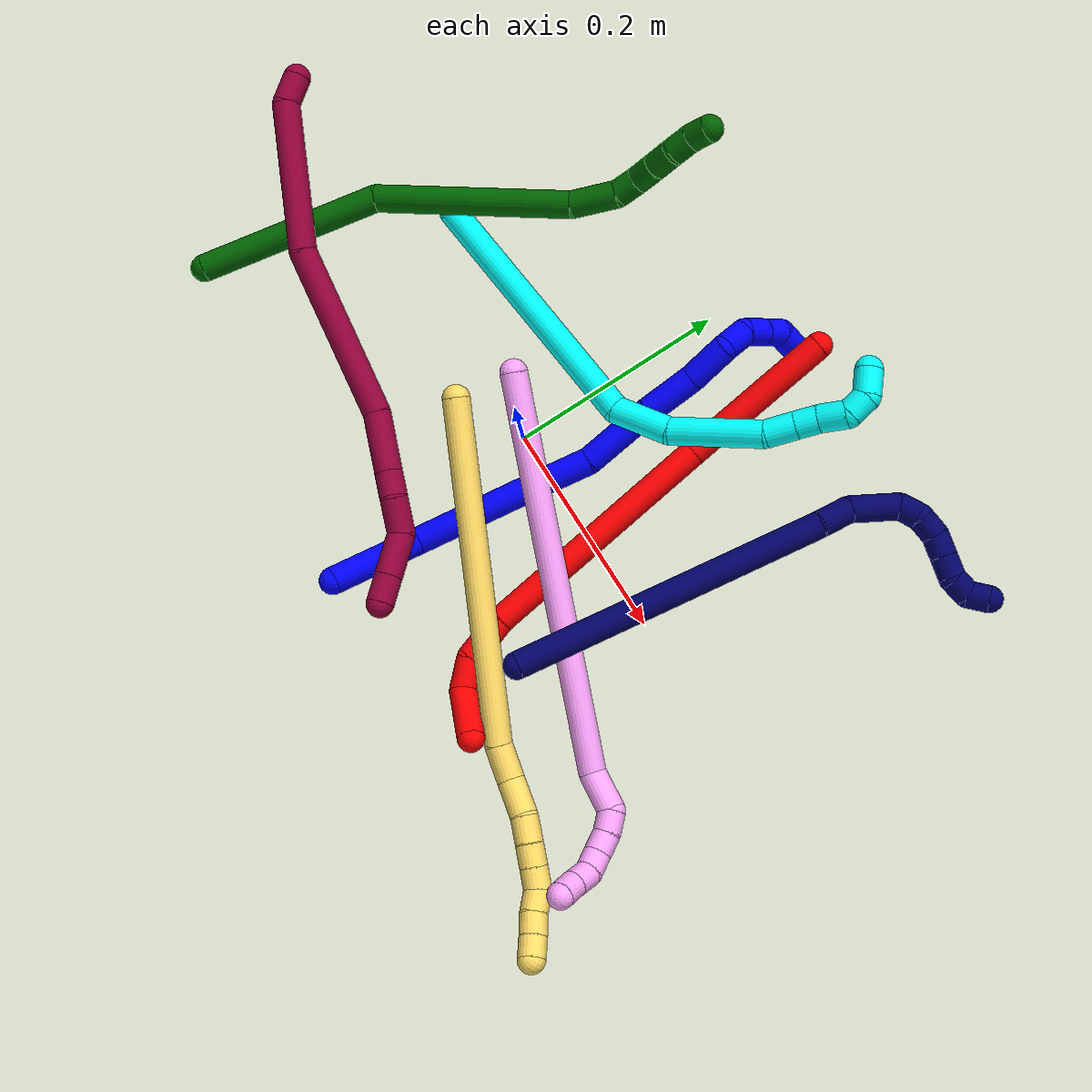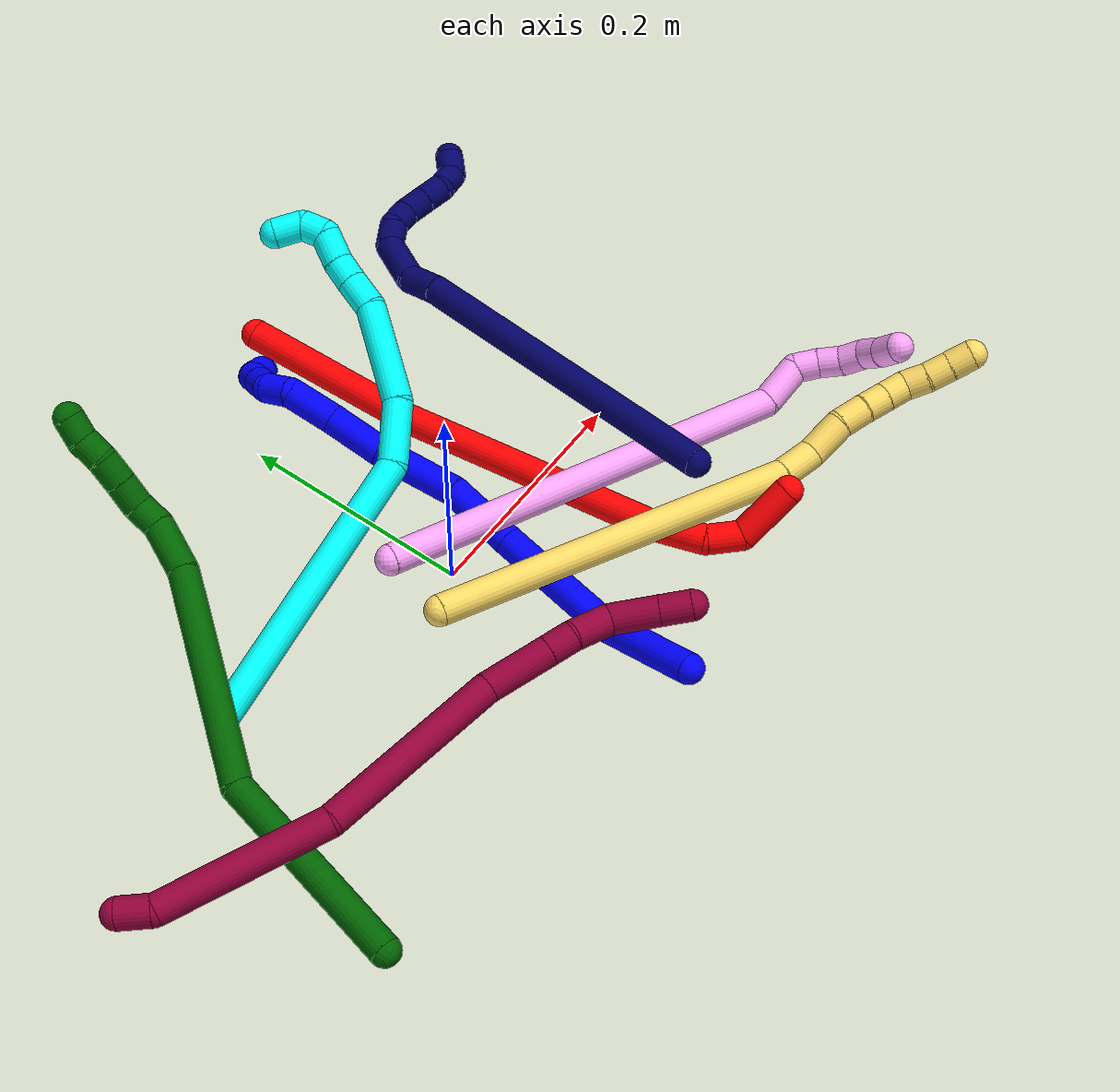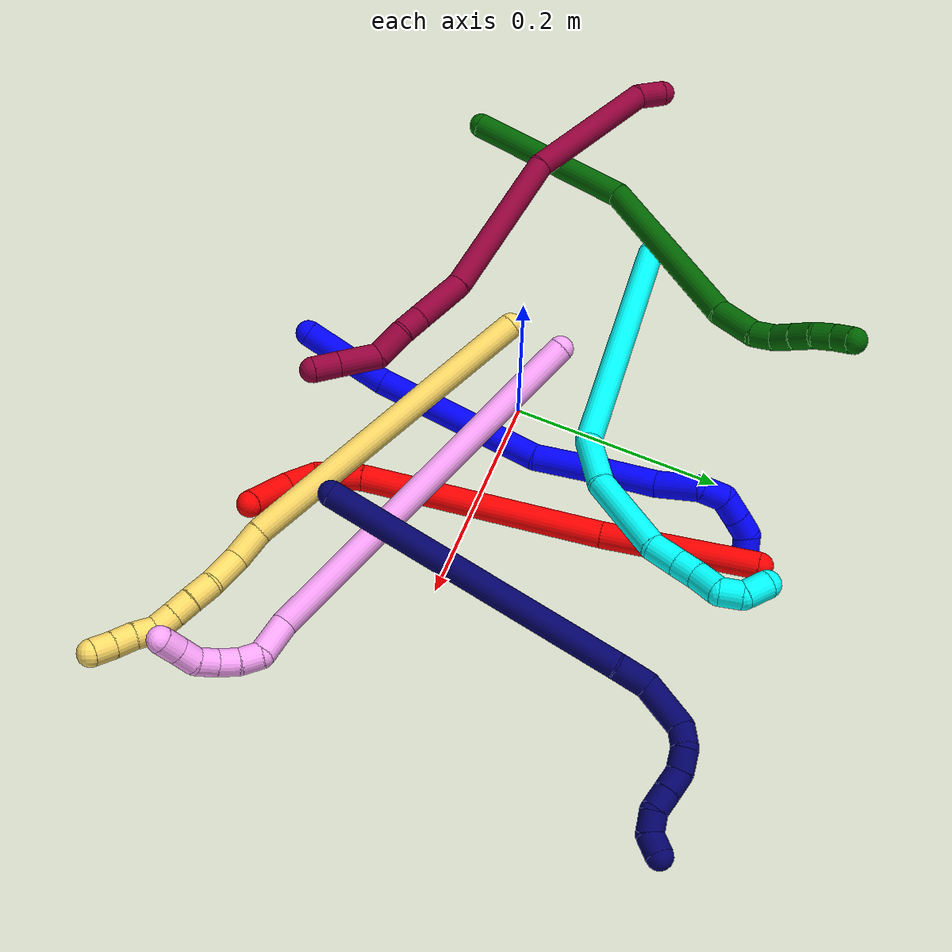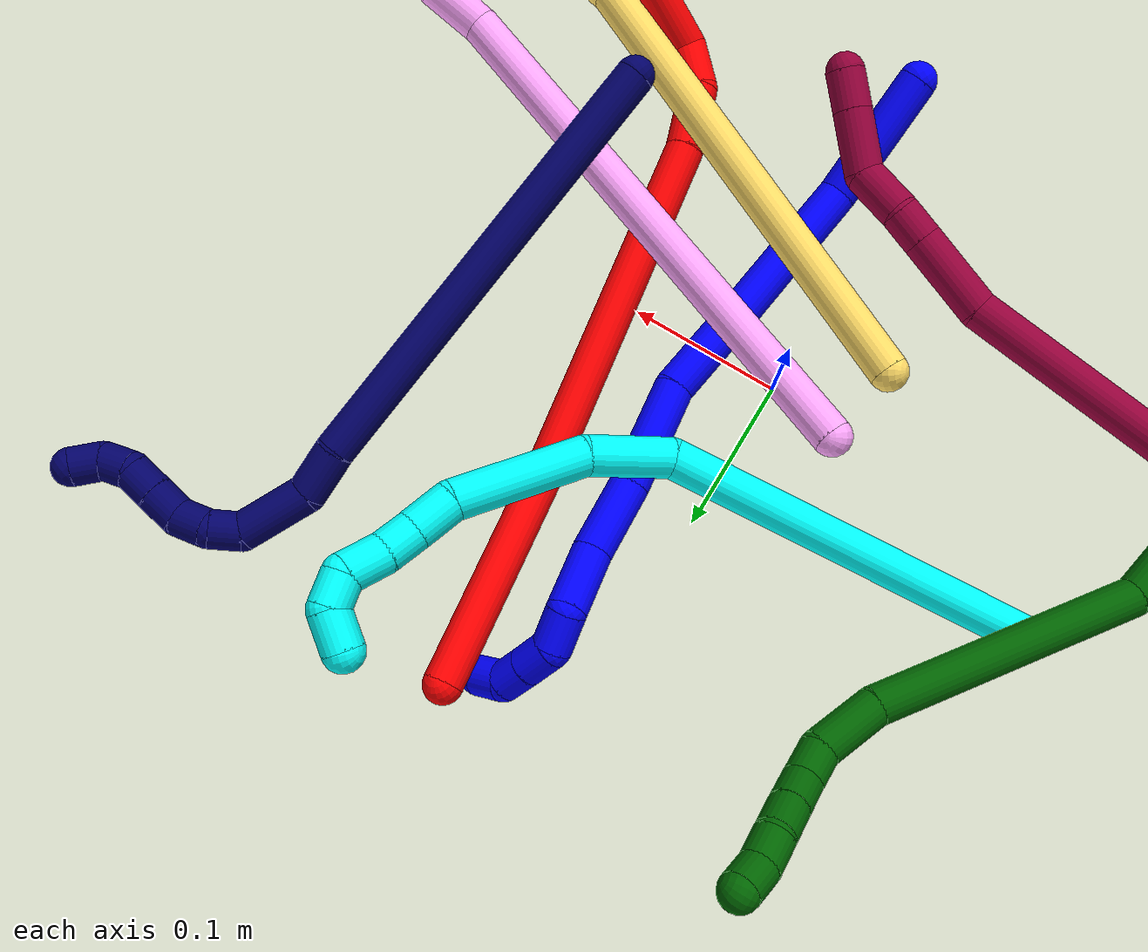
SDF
<sdf version="1.7">
 <world name="default">
  <plugin name="TubeGeneratorPlugin" filename="libtube_generator_plugin.so"/>
  <model name="photoneo_s_sensor">
   <static>1</static>
   <pose>0 0 2 1.57079 1.57079 3.14159</pose>
   <link name="link">
    <inertial><mass>0.1</mass></inertial>
    <sensor name="sensor" type="depth">
     <update_rate>30</update_rate>
     <camera>
      <horizontal_fov>1.22</horizontal_fov>
      <image><width>1920</width><height>1200</height><format>B8G8R8</format></image>
      <clip><near>0.1</near><far>4</far></clip>
      <depth_camera><output>points</output></depth_camera>
     </camera>
     <plugin name="camera_plugin" filename="libgazebo_ros_depth_camera.so">
      <baseline>0.2</baseline>
      <alwaysOn>1</alwaysOn>
      <updateRate>0.0</updateRate>
      <cameraName>camera_ir</cameraName>
      <imageTopicName>/camera/color/image_raw</imageTopicName>
      <cameraInfoTopicName>/camera/color/camera_info</cameraInfoTopicName>
      <depthImageTopicName>/camera/depth/image_raw</depthImageTopicName>
      <depthImageCameraInfoTopicName>/camera/depth/camera_info</depthImageCameraInfoTopicName>
      <pointCloudTopicName>/camera/depth/points</pointCloudTopicName>
      <frameName>fr_optical</frameName>
      <pointCloudCutoff>0.1</pointCloudCutoff>
      <pointCloudCutoffMax>2.0</pointCloudCutoffMax>
      <distortionK1>0</distortionK1>
      <distortionK2>0</distortionK2>
      <distortionK3>0</distortionK3>
      <distortionT1>0</distortionT1>
      <distortionT2>0</distortionT2>
      <CxPrime>0</CxPrime>
      <Cx>0</Cx>
      <Cy>0</Cy>
      <focalLength>0</focalLength>
      <hackBaseline>0</hackBaseline>
     </plugin>
    </sensor>
   </link>
  </model>
  <gravity>0 0 -9.8</gravity>
  <magnetic_field>6e-06 2.3e-05 -4.2e-05</magnetic_field>
  <atmosphere type="adiabatic"/>
  <physics name="default_physics" default="0" type="ode">
   <max_step_size>0.003</max_step_size>
   <real_time_factor>1</real_time_factor>
   <real_time_update_rate>1000</real_time_update_rate>
   <max_contacts>10000</max_contacts>
   <ode>
    <solver>
     <type>quick</type>
     <iters>100</iters>
     <sor>1.3</sor>
     <use_dynamic_moi_rescaling>0</use_dynamic_moi_rescaling>
    </solver>
    <constraints>
     <contact_max_correcting_vel>0</contact_max_correcting_vel>
     <contact_surface_layer>0.001</contact_surface_layer>
     <cfm>0</cfm>
     <erp>0.2</erp>
    </constraints>
   </ode>
  </physics>
  <scene><ambient>0.4 0.4 0.4 1</ambient><background>0.7 0.7 0.7 1</background><shadows>0</shadows></scene>
  <audio><device>default</device></audio>
  <spherical_coordinates>
   <surface_model>EARTH_WGS84</surface_model>
   <latitude_deg>0</latitude_deg>
   <longitude_deg>0</longitude_deg>
   <elevation>0</elevation>
   <heading_deg>0</heading_deg>
  </spherical_coordinates>
  <model name="bin">
   <static>1</static>
   <link name="bottom">
    <collision name="collision-bottom">
     <pose>0 0 -0.01 0 -0 0</pose>
     <geometry><box><size>0.8 0.6 0.02</size></box></geometry>
     <surface>
      <friction><ode><mu>100</mu><mu2>100</mu2></ode></friction>
      <contact><collide_bitmask>65535</collide_bitmask></contact>
     </surface>
    </collision>
   </link>
   <link name="west_wall">
    <collision name="collision-west_wall">
     <pose>-0.41 0 0.1 0 -0 0</pose>
     <geometry><box><size>0.02 0.6 0.2</size></box></geometry>
     <surface>
      <friction><ode><mu>100</mu><mu2>100</mu2></ode></friction>
      <contact><collide_bitmask>65535</collide_bitmask></contact>
     </surface>
    </collision>
   </link>
   <link name="east_wall">
    <collision name="collision-east_wall">
     <pose>0.41 0 0.1 0 -0 0</pose>
     <geometry><box><size>0.02 0.6 0.2</size></box></geometry>
     <surface>
      <friction><ode><mu>100</mu><mu2>100</mu2></ode></friction>
      <contact><collide_bitmask>65535</collide_bitmask></contact>
     </surface>
    </collision>
   </link>
   <link name="south_wall">
    <collision name="collision-south_wall">
     <pose>0 -0.31 0.1 0 -0 0</pose>
     <geometry><box><size>0.8 0.02 0.2</size></box></geometry>
     <surface>
      <friction><ode><mu>100</mu><mu2>100</mu2></ode></friction>
      <contact><collide_bitmask>65535</collide_bitmask></contact>
     </surface>
    </collision>
   </link>
   <link name="north_wall">
    <collision name="collision-north_wall">
     <pose>0 0.31 0.1 0 -0 0</pose>
     <geometry><box><size>0.8 0.02 0.2</size></box></geometry>
     <surface>
      <friction><ode><mu>100</mu><mu2>100</mu2></ode></friction>
      <contact><collide_bitmask>65535</collide_bitmask></contact>
     </surface>
    </collision>
   </link>
  </model>
  <model name="1">
   <static>0</static>
   <link name="1">
    <collision name="collision-cylinder-e_1_1_4">
     <pose>0.015067 0.008634 0.039076 -0.217461 0.360082 -0.039732</pose>
     <geometry><cylinder><radius>0.0125</radius><length>0.085523</length></cylinder></geometry>
     <surface>
      <friction><ode><mu>1.16</mu><mu2>1.16</mu2><slip1>0</slip1><slip2>0</slip2></ode></friction>
      <contact><ode><kp>1e+06</kp><kd>1</kd><max_vel>0</max_vel><min_depth>0.001</min_depth></ode></contact>
     </surface>
    </collision>
    <visual name="visual-cylinder-e_1_1_4">
     <pose>0.015067 0.008634 0.039076 -0.217461 0.360082 -0.039732</pose>
     <geometry><cylinder><radius>0.0125</radius><length>0.085523</length></cylinder></geometry>
     <material><ambient>0 0 1 1</ambient></material>
    </visual>
    <collision name="collision-cylinder-e_2_4_5">
     <pose>0.031209 0.039904 0.126933 -0.434463 0.01999 -0.004412</pose>
     <geometry><cylinder><radius>0.0125</radius><length>0.107573</length></cylinder></geometry>
     <surface>
      <friction><ode><mu>1.16</mu><mu2>1.16</mu2><slip1>0</slip1><slip2>0</slip2></ode></friction>
      <contact><ode><kp>1e+06</kp><kd>1</kd><max_vel>0</max_vel><min_depth>0.001</min_depth></ode></contact>
     </surface>
    </collision>
    <visual name="visual-cylinder-e_2_4_5">
     <pose>0.031209 0.039904 0.126933 -0.434463 0.01999 -0.004412</pose>
     <geometry><cylinder><radius>0.0125</radius><length>0.107573</length></cylinder></geometry>
     <material><ambient>0 0 1 1</ambient></material>
    </visual>
    <collision name="collision-cylinder-e_3_5_6">
     <pose>0.031936 0.075749 0.203781 -0.439862 -0.011226 0.00251</pose>
     <geometry><cylinder><radius>0.0125</radius><length>0.062047</length></cylinder></geometry>
     <surface>
      <friction><ode><mu>1.16</mu><mu2>1.16</mu2><slip1>0</slip1><slip2>0</slip2></ode></friction>
      <contact><ode><kp>1e+06</kp><kd>1</kd><max_vel>0</max_vel><min_depth>0.001</min_depth></ode></contact>
     </surface>
    </collision>
    <visual name="visual-cylinder-e_3_5_6">
     <pose>0.031936 0.075749 0.203781 -0.439862 -0.011226 0.00251</pose>
     <geometry><cylinder><radius>0.0125</radius><length>0.062047</length></cylinder></geometry>
     <material><ambient>0 0 1 1</ambient></material>
    </visual>
    <collision name="collision-cylinder-e_4_6_7">
     <pose>0.036293 0.110125 0.258727 -0.667091 0.136685 -0.047425</pose>
     <geometry><cylinder><radius>0.0125</radius><length>0.069066</length></cylinder></geometry>
     <surface>
      <friction><ode><mu>1.16</mu><mu2>1.16</mu2><slip1>0</slip1><slip2>0</slip2></ode></friction>
      <contact><ode><kp>1e+06</kp><kd>1</kd><max_vel>0</max_vel><min_depth>0.001</min_depth></ode></contact>
     </surface>
    </collision>
    <visual name="visual-cylinder-e_4_6_7">
     <pose>0.036293 0.110125 0.258727 -0.667091 0.136685 -0.047425</pose>
     <geometry><cylinder><radius>0.0125</radius><length>0.069066</length></cylinder></geometry>
     <material><ambient>0 0 1 1</ambient></material>
    </visual>
    <collision name="collision-cylinder-e_5_7_8">
     <pose>0.041806 0.145925 0.30478 -0.651869 0.033441 -0.011304</pose>
     <geometry><cylinder><radius>0.0125</radius><length>0.048271</length></cylinder></geometry>
     <surface>
      <friction><ode><mu>1.16</mu><mu2>1.16</mu2><slip1>0</slip1><slip2>0</slip2></ode></friction>
      <contact><ode><kp>1e+06</kp><kd>1</kd><max_vel>0</max_vel><min_depth>0.001</min_depth></ode></contact>
     </surface>
    </collision>
    <visual name="visual-cylinder-e_5_7_8">
     <pose>0.041806 0.145925 0.30478 -0.651869 0.033441 -0.011304</pose>
     <geometry><cylinder><radius>0.0125</radius><length>0.048271</length></cylinder></geometry>
     <material><ambient>0 0 1 1</ambient></material>
    </visual>
    <collision name="collision-cylinder-e_6_8_9">
     <pose>0.042638 0.174915 0.338025 -0.795486 0.001258 -0.000529</pose>
     <geometry><cylinder><radius>0.0125</radius><length>0.040201</length></cylinder></geometry>
     <surface>
      <friction><ode><mu>1.16</mu><mu2>1.16</mu2><slip1>0</slip1><slip2>0</slip2></ode></friction>
      <contact><ode><kp>1e+06</kp><kd>1</kd><max_vel>0</max_vel><min_depth>0.001</min_depth></ode></contact>
     </surface>
    </collision>
    <visual name="visual-cylinder-e_6_8_9">
     <pose>0.042638 0.174915 0.338025 -0.795486 0.001258 -0.000529</pose>
     <geometry><cylinder><radius>0.0125</radius><length>0.040201</length></cylinder></geometry>
     <material><ambient>0 0 1 1</ambient></material>
    </visual>
    <collision name="collision-cylinder-e_7_9_10">
     <pose>0.048729 0.193509 0.362 -0.404274 0.512714 -0.107334</pose>
     <geometry><cylinder><radius>0.0125</radius><length>0.02473</length></cylinder></geometry>
     <surface>
      <friction><ode><mu>1.16</mu><mu2>1.16</mu2><slip1>0</slip1><slip2>0</slip2></ode></friction>
      <contact><ode><kp>1e+06</kp><kd>1</kd><max_vel>0</max_vel><min_depth>0.001</min_depth></ode></contact>
     </surface>
    </collision>
    <visual name="visual-cylinder-e_7_9_10">
     <pose>0.048729 0.193509 0.362 -0.404274 0.512714 -0.107334</pose>
     <geometry><cylinder><radius>0.0125</radius><length>0.02473</length></cylinder></geometry>
     <material><ambient>0 0 1 1</ambient></material>
    </visual>
    <collision name="collision-cylinder-e_8_10_11">
     <pose>0.058828 0.195399 0.381961 0.229504 0.372406 0.043419</pose>
     <geometry><cylinder><radius>0.0125</radius><length>0.02217</length></cylinder></geometry>
     <surface>
      <friction><ode><mu>1.16</mu><mu2>1.16</mu2><slip1>0</slip1><slip2>0</slip2></ode></friction>
      <contact><ode><kp>1e+06</kp><kd>1</kd><max_vel>0</max_vel><min_depth>0.001</min_depth></ode></contact>
     </surface>
    </collision>
    <visual name="visual-cylinder-e_8_10_11">
     <pose>0.058828 0.195399 0.381961 0.229504 0.372406 0.043419</pose>
     <geometry><cylinder><radius>0.0125</radius><length>0.02217</length></cylinder></geometry>
     <material><ambient>0 0 1 1</ambient></material>
    </visual>
    <collision name="collision-cylinder-e_9_11_12">
     <pose>0.066553 0.190649 0.401105 0.258285 0.374198 0.04916</pose>
     <geometry><cylinder><radius>0.0125</radius><length>0.0202</length></cylinder></geometry>
     <surface>
      <friction><ode><mu>1.16</mu><mu2>1.16</mu2><slip1>0</slip1><slip2>0</slip2></ode></friction>
      <contact><ode><kp>1e+06</kp><kd>1</kd><max_vel>0</max_vel><min_depth>0.001</min_depth></ode></contact>
     </surface>
    </collision>
    <visual name="visual-cylinder-e_9_11_12">
     <pose>0.066553 0.190649 0.401105 0.258285 0.374198 0.04916</pose>
     <geometry><cylinder><radius>0.0125</radius><length>0.0202</length></cylinder></geometry>
     <material><ambient>0 0 1 1</ambient></material>
    </visual>
    <collision name="collision-cylinder-e_10_12_2">
     <pose>0.070958 0.1807 0.416882 0.845675 0.070661 0.031807</pose>
     <geometry><cylinder><radius>0.0125</radius><length>0.020219</length></cylinder></geometry>
     <surface>
      <friction><ode><mu>1.16</mu><mu2>1.16</mu2><slip1>0</slip1><slip2>0</slip2></ode></friction>
      <contact><ode><kp>1e+06</kp><kd>1</kd><max_vel>0</max_vel><min_depth>0.001</min_depth></ode></contact>
     </surface>
    </collision>
    <visual name="visual-cylinder-e_10_12_2">
     <pose>0.070958 0.1807 0.416882 0.845675 0.070661 0.031807</pose>
     <geometry><cylinder><radius>0.0125</radius><length>0.020219</length></cylinder></geometry>
     <material><ambient>0 0 1 1</ambient></material>
    </visual>
    <collision name="collision-sphere-2">
     <pose>0.071672 0.173153 0.42357 0 -0 0</pose>
     <geometry><sphere><radius>0.0125</radius></sphere></geometry>
     <surface>
      <friction><ode><mu>1.16</mu><mu2>1.16</mu2><slip1>0</slip1><slip2>0</slip2></ode></friction>
      <contact><ode><kp>1e+06</kp><kd>1</kd><max_vel>0</max_vel><min_depth>0.001</min_depth></ode></contact>
     </surface>
    </collision>
    <visual name="visual-sphere-2">
     <pose>0.071672 0.173153 0.42357 0 -0 0</pose>
     <geometry><sphere><radius>0.0125</radius></sphere></geometry>
     <material><ambient>0 0 1 1</ambient></material>
    </visual>
    <collision name="collision-sphere-12">
     <pose>0.070245 0.188247 0.410194 0 -0 0</pose>
     <geometry><sphere><radius>0.0125</radius></sphere></geometry>
     <surface>
      <friction><ode><mu>1.16</mu><mu2>1.16</mu2><slip1>0</slip1><slip2>0</slip2></ode></friction>
      <contact><ode><kp>1e+06</kp><kd>1</kd><max_vel>0</max_vel><min_depth>0.001</min_depth></ode></contact>
     </surface>
    </collision>
    <visual name="visual-sphere-12">
     <pose>0.070245 0.188247 0.410194 0 -0 0</pose>
     <geometry><sphere><radius>0.0125</radius></sphere></geometry>
     <material><ambient>0 0 1 1</ambient></material>
    </visual>
    <collision name="collision-sphere-11">
     <pose>0.062861 0.19305 0.392016 0 -0 0</pose>
     <geometry><sphere><radius>0.0125</radius></sphere></geometry>
     <surface>
      <friction><ode><mu>1.16</mu><mu2>1.16</mu2><slip1>0</slip1><slip2>0</slip2></ode></friction>
      <contact><ode><kp>1e+06</kp><kd>1</kd><max_vel>0</max_vel><min_depth>0.001</min_depth></ode></contact>
     </surface>
    </collision>
    <visual name="visual-sphere-11">
     <pose>0.062861 0.19305 0.392016 0 -0 0</pose>
     <geometry><sphere><radius>0.0125</radius></sphere></geometry>
     <material><ambient>0 0 1 1</ambient></material>
    </visual>
    <collision name="collision-sphere-10">
     <pose>0.054794 0.197748 0.371907 0 -0 0</pose>
     <geometry><sphere><radius>0.0125</radius></sphere></geometry>
     <surface>
      <friction><ode><mu>1.16</mu><mu2>1.16</mu2><slip1>0</slip1><slip2>0</slip2></ode></friction>
      <contact><ode><kp>1e+06</kp><kd>1</kd><max_vel>0</max_vel><min_depth>0.001</min_depth></ode></contact>
     </surface>
    </collision>
    <visual name="visual-sphere-10">
     <pose>0.054794 0.197748 0.371907 0 -0 0</pose>
     <geometry><sphere><radius>0.0125</radius></sphere></geometry>
     <material><ambient>0 0 1 1</ambient></material>
    </visual>
    <collision name="collision-sphere-9">
     <pose>0.042663 0.189271 0.352094 0 -0 0</pose>
     <geometry><sphere><radius>0.0125</radius></sphere></geometry>
     <surface>
      <friction><ode><mu>1.16</mu><mu2>1.16</mu2><slip1>0</slip1><slip2>0</slip2></ode></friction>
      <contact><ode><kp>1e+06</kp><kd>1</kd><max_vel>0</max_vel><min_depth>0.001</min_depth></ode></contact>
     </surface>
    </collision>
    <visual name="visual-sphere-9">
     <pose>0.042663 0.189271 0.352094 0 -0 0</pose>
     <geometry><sphere><radius>0.0125</radius></sphere></geometry>
     <material><ambient>0 0 1 1</ambient></material>
    </visual>
    <collision name="collision-sphere-4">
     <pose>0.030134 0.017268 0.078153 0 -0 0</pose>
     <geometry><sphere><radius>0.0125</radius></sphere></geometry>
     <surface>
      <friction><ode><mu>1.16</mu><mu2>1.16</mu2><slip1>0</slip1><slip2>0</slip2></ode></friction>
      <contact><ode><kp>1e+06</kp><kd>1</kd><max_vel>0</max_vel><min_depth>0.001</min_depth></ode></contact>
     </surface>
    </collision>
    <visual name="visual-sphere-4">
     <pose>0.030134 0.017268 0.078153 0 -0 0</pose>
     <geometry><sphere><radius>0.0125</radius></sphere></geometry>
     <material><ambient>0 0 1 1</ambient></material>
    </visual>
    <collision name="collision-sphere-1">
     <geometry><sphere><radius>0.0125</radius></sphere></geometry>
     <surface>
      <friction><ode><mu>1.16</mu><mu2>1.16</mu2><slip1>0</slip1><slip2>0</slip2></ode></friction>
      <contact><ode><kp>1e+06</kp><kd>1</kd><max_vel>0</max_vel><min_depth>0.001</min_depth></ode></contact>
     </surface>
    </collision>
    <visual name="visual-sphere-1">
     <geometry><sphere><radius>0.0125</radius></sphere></geometry>
     <material><ambient>0 0 1 1</ambient></material>
    </visual>
    <collision name="collision-sphere-8">
     <pose>0.042613 0.160559 0.323956 0 -0 0</pose>
     <geometry><sphere><radius>0.0125</radius></sphere></geometry>
     <surface>
      <friction><ode><mu>1.16</mu><mu2>1.16</mu2><slip1>0</slip1><slip2>0</slip2></ode></friction>
      <contact><ode><kp>1e+06</kp><kd>1</kd><max_vel>0</max_vel><min_depth>0.001</min_depth></ode></contact>
     </surface>
    </collision>
    <visual name="visual-sphere-8">
     <pose>0.042613 0.160559 0.323956 0 -0 0</pose>
     <geometry><sphere><radius>0.0125</radius></sphere></geometry>
     <material><ambient>0 0 1 1</ambient></material>
    </visual>
    <collision name="collision-sphere-5">
     <pose>0.032284 0.062539 0.175713 0 -0 0</pose>
     <geometry><sphere><radius>0.0125</radius></sphere></geometry>
     <surface>
      <friction><ode><mu>1.16</mu><mu2>1.16</mu2><slip1>0</slip1><slip2>0</slip2></ode></friction>
      <contact><ode><kp>1e+06</kp><kd>1</kd><max_vel>0</max_vel><min_depth>0.001</min_depth></ode></contact>
     </surface>
    </collision>
    <visual name="visual-sphere-5">
     <pose>0.032284 0.062539 0.175713 0 -0 0</pose>
     <geometry><sphere><radius>0.0125</radius></sphere></geometry>
     <material><ambient>0 0 1 1</ambient></material>
    </visual>
    <collision name="collision-sphere-6">
     <pose>0.031588 0.088958 0.23185 0 -0 0</pose>
     <geometry><sphere><radius>0.0125</radius></sphere></geometry>
     <surface>
      <friction><ode><mu>1.16</mu><mu2>1.16</mu2><slip1>0</slip1><slip2>0</slip2></ode></friction>
      <contact><ode><kp>1e+06</kp><kd>1</kd><max_vel>0</max_vel><min_depth>0.001</min_depth></ode></contact>
     </surface>
    </collision>
    <visual name="visual-sphere-6">
     <pose>0.031588 0.088958 0.23185 0 -0 0</pose>
     <geometry><sphere><radius>0.0125</radius></sphere></geometry>
     <material><ambient>0 0 1 1</ambient></material>
    </visual>
    <collision name="collision-sphere-7">
     <pose>0.040999 0.131291 0.285604 0 -0 0</pose>
     <geometry><sphere><radius>0.0125</radius></sphere></geometry>
     <surface>
      <friction><ode><mu>1.16</mu><mu2>1.16</mu2><slip1>0</slip1><slip2>0</slip2></ode></friction>
      <contact><ode><kp>1e+06</kp><kd>1</kd><max_vel>0</max_vel><min_depth>0.001</min_depth></ode></contact>
     </surface>
    </collision>
    <visual name="visual-sphere-7">
     <pose>0.040999 0.131291 0.285604 0 -0 0</pose>
     <geometry><sphere><radius>0.0125</radius></sphere></geometry>
     <material><ambient>0 0 1 1</ambient></material>
    </visual>
    <inertial>
     <pose>0.036309 0.096069 0.219525 0 -0 0</pose>
     <mass>0.5</mass>
     <inertia>
      <ixx>0.000238</ixx>
      <ixy>0</ixy>
      <ixz>0</ixz>
      <iyy>0.000226</iyy>
      <iyz>0</iyz>
      <izz>-9.1e-05</izz>
     </inertia>
    </inertial>
   </link>
   <pose>0.019928 -0.210885 0.038469 1.84617 0.933383 2.8656</pose>
  </model>
  <model name="2">
   <static>0</static>
   <link name="2">
    <collision name="collision-cylinder-e_1_1_4">
     <pose>0.048579 -0.054043 -0.01039 1.76073 0.72319 0.858748</pose>
     <geometry><cylinder><radius>0.0125</radius><length>0.146814</length></cylinder></geometry>
     <surface>
      <friction><ode><mu>1.16</mu><mu2>1.16</mu2><slip1>0</slip1><slip2>0</slip2></ode></friction>
      <contact><ode><kp>1e+06</kp><kd>1</kd><max_vel>0</max_vel><min_depth>0.001</min_depth></ode></contact>
     </surface>
    </collision>
    <visual name="visual-cylinder-e_1_1_4">
     <pose>0.048579 -0.054043 -0.01039 1.76073 0.72319 0.858748</pose>
     <geometry><cylinder><radius>0.0125</radius><length>0.146814</length></cylinder></geometry>
     <material><ambient>1 0 0 1</ambient></material>
    </visual>
    <collision name="collision-cylinder-e_2_4_5">
     <pose>0.174796 -0.185826 -0.052889 1.96249 0.745404 1.05789</pose>
     <geometry><cylinder><radius>0.0125</radius><length>0.228929</length></cylinder></geometry>
     <surface>
      <friction><ode><mu>1.16</mu><mu2>1.16</mu2><slip1>0</slip1><slip2>0</slip2></ode></friction>
      <contact><ode><kp>1e+06</kp><kd>1</kd><max_vel>0</max_vel><min_depth>0.001</min_depth></ode></contact>
     </surface>
    </collision>
    <visual name="visual-cylinder-e_2_4_5">
     <pose>0.174796 -0.185826 -0.052889 1.96249 0.745404 1.05789</pose>
     <geometry><cylinder><radius>0.0125</radius><length>0.228929</length></cylinder></geometry>
     <material><ambient>1 0 0 1</ambient></material>
    </visual>
    <collision name="collision-cylinder-e_3_5_6">
     <pose>0.264066 -0.280169 -0.092404 1.99032 0.569236 0.847078</pose>
     <geometry><cylinder><radius>0.0125</radius><length>0.043165</length></cylinder></geometry>
     <surface>
      <friction><ode><mu>1.16</mu><mu2>1.16</mu2><slip1>0</slip1><slip2>0</slip2></ode></friction>
      <contact><ode><kp>1e+06</kp><kd>1</kd><max_vel>0</max_vel><min_depth>0.001</min_depth></ode></contact>
     </surface>
    </collision>
    <visual name="visual-cylinder-e_3_5_6">
     <pose>0.264066 -0.280169 -0.092404 1.99032 0.569236 0.847078</pose>
     <geometry><cylinder><radius>0.0125</radius><length>0.043165</length></cylinder></geometry>
     <material><ambient>1 0 0 1</ambient></material>
    </visual>
    <collision name="collision-cylinder-e_4_6_7">
     <pose>0.277497 -0.309853 -0.107132 2.08112 0.119362 0.20315</pose>
     <geometry><cylinder><radius>0.0125</radius><length>0.030199</length></cylinder></geometry>
     <surface>
      <friction><ode><mu>1.16</mu><mu2>1.16</mu2><slip1>0</slip1><slip2>0</slip2></ode></friction>
      <contact><ode><kp>1e+06</kp><kd>1</kd><max_vel>0</max_vel><min_depth>0.001</min_depth></ode></contact>
     </surface>
    </collision>
    <visual name="visual-cylinder-e_4_6_7">
     <pose>0.277497 -0.309853 -0.107132 2.08112 0.119362 0.20315</pose>
     <geometry><cylinder><radius>0.0125</radius><length>0.030199</length></cylinder></geometry>
     <material><ambient>1 0 0 1</ambient></material>
    </visual>
    <collision name="collision-cylinder-e_5_7_2">
     <pose>0.274806 -0.332598 -0.137564 2.74556 -0.177355 -0.834242</pose>
     <geometry><cylinder><radius>0.0125</radius><length>0.050894</length></cylinder></geometry>
     <surface>
      <friction><ode><mu>1.16</mu><mu2>1.16</mu2><slip1>0</slip1><slip2>0</slip2></ode></friction>
      <contact><ode><kp>1e+06</kp><kd>1</kd><max_vel>0</max_vel><min_depth>0.001</min_depth></ode></contact>
     </surface>
    </collision>
    <visual name="visual-cylinder-e_5_7_2">
     <pose>0.274806 -0.332598 -0.137564 2.74556 -0.177355 -0.834242</pose>
     <geometry><cylinder><radius>0.0125</radius><length>0.050894</length></cylinder></geometry>
     <material><ambient>1 0 0 1</ambient></material>
    </visual>
    <collision name="collision-sphere-2">
     <pose>0.270316 -0.34226 -0.160673 0 -0 0</pose>
     <geometry><sphere><radius>0.0125</radius></sphere></geometry>
     <surface>
      <friction><ode><mu>1.16</mu><mu2>1.16</mu2><slip1>0</slip1><slip2>0</slip2></ode></friction>
      <contact><ode><kp>1e+06</kp><kd>1</kd><max_vel>0</max_vel><min_depth>0.001</min_depth></ode></contact>
     </surface>
    </collision>
    <visual name="visual-sphere-2">
     <pose>0.270316 -0.34226 -0.160673 0 -0 0</pose>
     <geometry><sphere><radius>0.0125</radius></sphere></geometry>
     <material><ambient>1 0 0 1</ambient></material>
    </visual>
    <collision name="collision-sphere-7">
     <pose>0.279295 -0.322935 -0.114455 0 -0 0</pose>
     <geometry><sphere><radius>0.0125</radius></sphere></geometry>
     <surface>
      <friction><ode><mu>1.16</mu><mu2>1.16</mu2><slip1>0</slip1><slip2>0</slip2></ode></friction>
      <contact><ode><kp>1e+06</kp><kd>1</kd><max_vel>0</max_vel><min_depth>0.001</min_depth></ode></contact>
     </surface>
    </collision>
    <visual name="visual-sphere-7">
     <pose>0.279295 -0.322935 -0.114455 0 -0 0</pose>
     <geometry><sphere><radius>0.0125</radius></sphere></geometry>
     <material><ambient>1 0 0 1</ambient></material>
    </visual>
    <collision name="collision-sphere-6">
     <pose>0.275699 -0.296772 -0.099809 0 -0 0</pose>
     <geometry><sphere><radius>0.0125</radius></sphere></geometry>
     <surface>
      <friction><ode><mu>1.16</mu><mu2>1.16</mu2><slip1>0</slip1><slip2>0</slip2></ode></friction>
      <contact><ode><kp>1e+06</kp><kd>1</kd><max_vel>0</max_vel><min_depth>0.001</min_depth></ode></contact>
     </surface>
    </collision>
    <visual name="visual-sphere-6">
     <pose>0.275699 -0.296772 -0.099809 0 -0 0</pose>
     <geometry><sphere><radius>0.0125</radius></sphere></geometry>
     <material><ambient>1 0 0 1</ambient></material>
    </visual>
    <collision name="collision-sphere-5">
     <pose>0.252434 -0.263566 -0.084999 0 -0 0</pose>
     <geometry><sphere><radius>0.0125</radius></sphere></geometry>
     <surface>
      <friction><ode><mu>1.16</mu><mu2>1.16</mu2><slip1>0</slip1><slip2>0</slip2></ode></friction>
      <contact><ode><kp>1e+06</kp><kd>1</kd><max_vel>0</max_vel><min_depth>0.001</min_depth></ode></contact>
     </surface>
    </collision>
    <visual name="visual-sphere-5">
     <pose>0.252434 -0.263566 -0.084999 0 -0 0</pose>
     <geometry><sphere><radius>0.0125</radius></sphere></geometry>
     <material><ambient>1 0 0 1</ambient></material>
    </visual>
    <collision name="collision-sphere-1">
     <geometry><sphere><radius>0.0125</radius></sphere></geometry>
     <surface>
      <friction><ode><mu>1.16</mu><mu2>1.16</mu2><slip1>0</slip1><slip2>0</slip2></ode></friction>
      <contact><ode><kp>1e+06</kp><kd>1</kd><max_vel>0</max_vel><min_depth>0.001</min_depth></ode></contact>
     </surface>
    </collision>
    <visual name="visual-sphere-1">
     <geometry><sphere><radius>0.0125</radius></sphere></geometry>
     <material><ambient>1 0 0 1</ambient></material>
    </visual>
    <collision name="collision-sphere-4">
     <pose>0.097158 -0.108087 -0.020779 0 -0 0</pose>
     <geometry><sphere><radius>0.0125</radius></sphere></geometry>
     <surface>
      <friction><ode><mu>1.16</mu><mu2>1.16</mu2><slip1>0</slip1><slip2>0</slip2></ode></friction>
      <contact><ode><kp>1e+06</kp><kd>1</kd><max_vel>0</max_vel><min_depth>0.001</min_depth></ode></contact>
     </surface>
    </collision>
    <visual name="visual-sphere-4">
     <pose>0.097158 -0.108087 -0.020779 0 -0 0</pose>
     <geometry><sphere><radius>0.0125</radius></sphere></geometry>
     <material><ambient>1 0 0 1</ambient></material>
    </visual>
    <inertial>
     <pose>0.161825 -0.177706 -0.055716 0 -0 0</pose>
     <mass>0.5</mass>
     <inertia><ixx>0.001329</ixx><ixy>0</ixy><ixz>0</ixz><iyy>0.001222</iyy><iyz>0</iyz><izz>2e-05</izz></inertia>
    </inertial>
   </link>
   <pose>0.076648 0.264731 0.035551 2.61171 -0.141455 -2.24173</pose>
  </model>
  <model name="3">
   <static>0</static>
   <link name="3">
    <collision name="collision-cylinder-e_1_1_4">
     <pose>0.074368 -0.038583 -0.087111 2.72465 0.662787 2.03911</pose>
     <geometry><cylinder><radius>0.0125</radius><length>0.241723</length></cylinder></geometry>
     <surface>
      <friction><ode><mu>1.16</mu><mu2>1.16</mu2><slip1>0</slip1><slip2>0</slip2></ode></friction>
      <contact><ode><kp>1e+06</kp><kd>1</kd><max_vel>0</max_vel><min_depth>0.001</min_depth></ode></contact>
     </surface>
    </collision>
    <visual name="visual-cylinder-e_1_1_4">
     <pose>0.074368 -0.038583 -0.087111 2.72465 0.662787 2.03911</pose>
     <geometry><cylinder><radius>0.0125</radius><length>0.241723</length></cylinder></geometry>
     <material><ambient>0.003922 1 0.996078 1</ambient></material>
    </visual>
    <collision name="collision-cylinder-e_2_4_5">
     <pose>0.165854 -0.072776 -0.194533 -2.92875 0.689072 -2.56293</pose>
     <geometry><cylinder><radius>0.0125</radius><length>0.053846</length></cylinder></geometry>
     <surface>
      <friction><ode><mu>1.16</mu><mu2>1.16</mu2><slip1>0</slip1><slip2>0</slip2></ode></friction>
      <contact><ode><kp>1e+06</kp><kd>1</kd><max_vel>0</max_vel><min_depth>0.001</min_depth></ode></contact>
     </surface>
    </collision>
    <visual name="visual-cylinder-e_2_4_5">
     <pose>0.165854 -0.072776 -0.194533 -2.92875 0.689072 -2.56293</pose>
     <geometry><cylinder><radius>0.0125</radius><length>0.053846</length></cylinder></geometry>
     <material><ambient>0.003922 1 0.996078 1</ambient></material>
    </visual>
    <collision name="collision-cylinder-e_3_5_6">
     <pose>0.20387 -0.048628 -0.246108 -2.57798 0.514315 -1.47483</pose>
     <geometry><cylinder><radius>0.0125</radius><length>0.084959</length></cylinder></geometry>
     <surface>
      <friction><ode><mu>1.16</mu><mu2>1.16</mu2><slip1>0</slip1><slip2>0</slip2></ode></friction>
      <contact><ode><kp>1e+06</kp><kd>1</kd><max_vel>0</max_vel><min_depth>0.001</min_depth></ode></contact>
     </surface>
    </collision>
    <visual name="visual-cylinder-e_3_5_6">
     <pose>0.20387 -0.048628 -0.246108 -2.57798 0.514315 -1.47483</pose>
     <geometry><cylinder><radius>0.0125</radius><length>0.084959</length></cylinder></geometry>
     <material><ambient>0.003922 1 0.996078 1</ambient></material>
    </visual>
    <collision name="collision-cylinder-e_4_6_7">
     <pose>0.228406 -0.01923 -0.286403 -2.32365 0.268788 -0.604799</pose>
     <geometry><cylinder><radius>0.0125</radius><length>0.027405</length></cylinder></geometry>
     <surface>
      <friction><ode><mu>1.16</mu><mu2>1.16</mu2><slip1>0</slip1><slip2>0</slip2></ode></friction>
      <contact><ode><kp>1e+06</kp><kd>1</kd><max_vel>0</max_vel><min_depth>0.001</min_depth></ode></contact>
     </surface>
    </collision>
    <visual name="visual-cylinder-e_4_6_7">
     <pose>0.228406 -0.01923 -0.286403 -2.32365 0.268788 -0.604799</pose>
     <geometry><cylinder><radius>0.0125</radius><length>0.027405</length></cylinder></geometry>
     <material><ambient>0.003922 1 0.996078 1</ambient></material>
    </visual>
    <collision name="collision-cylinder-e_5_7_8">
     <pose>0.235376 -0.002199 -0.302131 -2.30693 0.322376 -0.702998</pose>
     <geometry><cylinder><radius>0.0125</radius><length>0.021028</length></cylinder></geometry>
     <surface>
      <friction><ode><mu>1.16</mu><mu2>1.16</mu2><slip1>0</slip1><slip2>0</slip2></ode></friction>
      <contact><ode><kp>1e+06</kp><kd>1</kd><max_vel>0</max_vel><min_depth>0.001</min_depth></ode></contact>
     </surface>
    </collision>
    <visual name="visual-cylinder-e_5_7_8">
     <pose>0.235376 -0.002199 -0.302131 -2.30693 0.322376 -0.702998</pose>
     <geometry><cylinder><radius>0.0125</radius><length>0.021028</length></cylinder></geometry>
     <material><ambient>0.003922 1 0.996078 1</ambient></material>
    </visual>
    <collision name="collision-cylinder-e_6_8_9">
     <pose>0.245374 0.013328 -0.316676 -2.33817 0.532834 -1.14204</pose>
     <geometry><cylinder><radius>0.0125</radius><length>0.02625</length></cylinder></geometry>
     <surface>
      <friction><ode><mu>1.16</mu><mu2>1.16</mu2><slip1>0</slip1><slip2>0</slip2></ode></friction>
      <contact><ode><kp>1e+06</kp><kd>1</kd><max_vel>0</max_vel><min_depth>0.001</min_depth></ode></contact>
     </surface>
    </collision>
    <visual name="visual-cylinder-e_6_8_9">
     <pose>0.245374 0.013328 -0.316676 -2.33817 0.532834 -1.14204</pose>
     <geometry><cylinder><radius>0.0125</radius><length>0.02625</length></cylinder></geometry>
     <material><ambient>0.003922 1 0.996078 1</ambient></material>
    </visual>
    <collision name="collision-cylinder-e_7_9_10">
     <pose>0.251211 0.031014 -0.328239 -1.94173 -0.080884 0.118172</pose>
     <geometry><cylinder><radius>0.0125</radius><length>0.02056</length></cylinder></geometry>
     <surface>
      <friction><ode><mu>1.16</mu><mu2>1.16</mu2><slip1>0</slip1><slip2>0</slip2></ode></friction>
      <contact><ode><kp>1e+06</kp><kd>1</kd><max_vel>0</max_vel><min_depth>0.001</min_depth></ode></contact>
     </surface>
    </collision>
    <visual name="visual-cylinder-e_7_9_10">
     <pose>0.251211 0.031014 -0.328239 -1.94173 -0.080884 0.118172</pose>
     <geometry><cylinder><radius>0.0125</radius><length>0.02056</length></cylinder></geometry>
     <material><ambient>0.003922 1 0.996078 1</ambient></material>
    </visual>
    <collision name="collision-cylinder-e_8_10_2">
     <pose>0.243908 0.050591 -0.329874 -1.36641 -0.563623 0.462876</pose>
     <geometry><cylinder><radius>0.0125</radius><length>0.02423</length></cylinder></geometry>
     <surface>
      <friction><ode><mu>1.16</mu><mu2>1.16</mu2><slip1>0</slip1><slip2>0</slip2></ode></friction>
      <contact><ode><kp>1e+06</kp><kd>1</kd><max_vel>0</max_vel><min_depth>0.001</min_depth></ode></contact>
     </surface>
    </collision>
    <visual name="visual-cylinder-e_8_10_2">
     <pose>0.243908 0.050591 -0.329874 -1.36641 -0.563623 0.462876</pose>
     <geometry><cylinder><radius>0.0125</radius><length>0.02423</length></cylinder></geometry>
     <material><ambient>0.003922 1 0.996078 1</ambient></material>
    </visual>
    <collision name="collision-sphere-2">
     <pose>0.237435 0.060619 -0.327796 0 -0 0</pose>
     <geometry><sphere><radius>0.0125</radius></sphere></geometry>
     <surface>
      <friction><ode><mu>1.16</mu><mu2>1.16</mu2><slip1>0</slip1><slip2>0</slip2></ode></friction>
      <contact><ode><kp>1e+06</kp><kd>1</kd><max_vel>0</max_vel><min_depth>0.001</min_depth></ode></contact>
     </surface>
    </collision>
    <visual name="visual-sphere-2">
     <pose>0.237435 0.060619 -0.327796 0 -0 0</pose>
     <geometry><sphere><radius>0.0125</radius></sphere></geometry>
     <material><ambient>0.003922 1 0.996078 1</ambient></material>
    </visual>
    <collision name="collision-sphere-10">
     <pose>0.25038 0.040564 -0.331953 0 -0 0</pose>
     <geometry><sphere><radius>0.0125</radius></sphere></geometry>
     <surface>
      <friction><ode><mu>1.16</mu><mu2>1.16</mu2><slip1>0</slip1><slip2>0</slip2></ode></friction>
      <contact><ode><kp>1e+06</kp><kd>1</kd><max_vel>0</max_vel><min_depth>0.001</min_depth></ode></contact>
     </surface>
    </collision>
    <visual name="visual-sphere-10">
     <pose>0.25038 0.040564 -0.331953 0 -0 0</pose>
     <geometry><sphere><radius>0.0125</radius></sphere></geometry>
     <material><ambient>0.003922 1 0.996078 1</ambient></material>
    </visual>
    <collision name="collision-sphere-9">
     <pose>0.252041 0.021465 -0.324524 0 -0 0</pose>
     <geometry><sphere><radius>0.0125</radius></sphere></geometry>
     <surface>
      <friction><ode><mu>1.16</mu><mu2>1.16</mu2><slip1>0</slip1><slip2>0</slip2></ode></friction>
      <contact><ode><kp>1e+06</kp><kd>1</kd><max_vel>0</max_vel><min_depth>0.001</min_depth></ode></contact>
     </surface>
    </collision>
    <visual name="visual-sphere-9">
     <pose>0.252041 0.021465 -0.324524 0 -0 0</pose>
     <geometry><sphere><radius>0.0125</radius></sphere></geometry>
     <material><ambient>0.003922 1 0.996078 1</ambient></material>
    </visual>
    <collision name="collision-sphere-4">
     <pose>0.148736 -0.077166 -0.174221 0 -0 0</pose>
     <geometry><sphere><radius>0.0125</radius></sphere></geometry>
     <surface>
      <friction><ode><mu>1.16</mu><mu2>1.16</mu2><slip1>0</slip1><slip2>0</slip2></ode></friction>
      <contact><ode><kp>1e+06</kp><kd>1</kd><max_vel>0</max_vel><min_depth>0.001</min_depth></ode></contact>
     </surface>
    </collision>
    <visual name="visual-sphere-4">
     <pose>0.148736 -0.077166 -0.174221 0 -0 0</pose>
     <geometry><sphere><radius>0.0125</radius></sphere></geometry>
     <material><ambient>0.003922 1 0.996078 1</ambient></material>
    </visual>
    <collision name="collision-sphere-1">
     <geometry><sphere><radius>0.0125</radius></sphere></geometry>
     <surface>
      <friction><ode><mu>1.16</mu><mu2>1.16</mu2><slip1>0</slip1><slip2>0</slip2></ode></friction>
      <contact><ode><kp>1e+06</kp><kd>1</kd><max_vel>0</max_vel><min_depth>0.001</min_depth></ode></contact>
     </surface>
    </collision>
    <visual name="visual-sphere-1">
     <geometry><sphere><radius>0.0125</radius></sphere></geometry>
     <material><ambient>0.003922 1 0.996078 1</ambient></material>
    </visual>
    <collision name="collision-sphere-8">
     <pose>0.238707 0.005191 -0.308827 0 -0 0</pose>
     <geometry><sphere><radius>0.0125</radius></sphere></geometry>
     <surface>
      <friction><ode><mu>1.16</mu><mu2>1.16</mu2><slip1>0</slip1><slip2>0</slip2></ode></friction>
      <contact><ode><kp>1e+06</kp><kd>1</kd><max_vel>0</max_vel><min_depth>0.001</min_depth></ode></contact>
     </surface>
    </collision>
    <visual name="visual-sphere-8">
     <pose>0.238707 0.005191 -0.308827 0 -0 0</pose>
     <geometry><sphere><radius>0.0125</radius></sphere></geometry>
     <material><ambient>0.003922 1 0.996078 1</ambient></material>
    </visual>
    <collision name="collision-sphere-5">
     <pose>0.182973 -0.068387 -0.214844 0 -0 0</pose>
     <geometry><sphere><radius>0.0125</radius></sphere></geometry>
     <surface>
      <friction><ode><mu>1.16</mu><mu2>1.16</mu2><slip1>0</slip1><slip2>0</slip2></ode></friction>
      <contact><ode><kp>1e+06</kp><kd>1</kd><max_vel>0</max_vel><min_depth>0.001</min_depth></ode></contact>
     </surface>
    </collision>
    <visual name="visual-sphere-5">
     <pose>0.182973 -0.068387 -0.214844 0 -0 0</pose>
     <geometry><sphere><radius>0.0125</radius></sphere></geometry>
     <material><ambient>0.003922 1 0.996078 1</ambient></material>
    </visual>
    <collision name="collision-sphere-6">
     <pose>0.224767 -0.02887 -0.277371 0 -0 0</pose>
     <geometry><sphere><radius>0.0125</radius></sphere></geometry>
     <surface>
      <friction><ode><mu>1.16</mu><mu2>1.16</mu2><slip1>0</slip1><slip2>0</slip2></ode></friction>
      <contact><ode><kp>1e+06</kp><kd>1</kd><max_vel>0</max_vel><min_depth>0.001</min_depth></ode></contact>
     </surface>
    </collision>
    <visual name="visual-sphere-6">
     <pose>0.224767 -0.02887 -0.277371 0 -0 0</pose>
     <geometry><sphere><radius>0.0125</radius></sphere></geometry>
     <material><ambient>0.003922 1 0.996078 1</ambient></material>
    </visual>
    <collision name="collision-sphere-7">
     <pose>0.232045 -0.009589 -0.295436 0 -0 0</pose>
     <geometry><sphere><radius>0.0125</radius></sphere></geometry>
     <surface>
      <friction><ode><mu>1.16</mu><mu2>1.16</mu2><slip1>0</slip1><slip2>0</slip2></ode></friction>
      <contact><ode><kp>1e+06</kp><kd>1</kd><max_vel>0</max_vel><min_depth>0.001</min_depth></ode></contact>
     </surface>
    </collision>
    <visual name="visual-sphere-7">
     <pose>0.232045 -0.009589 -0.295436 0 -0 0</pose>
     <geometry><sphere><radius>0.0125</radius></sphere></geometry>
     <material><ambient>0.003922 1 0.996078 1</ambient></material>
    </visual>
    <inertial>
     <pose>0.145904 -0.031473 -0.179393 0 -0 0</pose>
     <mass>0.5</mass>
     <inertia>
      <ixx>0.000376</ixx>
      <ixy>0</ixy>
      <ixz>0</ixz>
      <iyy>0.001558</iyy>
      <iyz>0</iyz>
      <izz>-0.00045</izz>
     </inertia>
    </inertial>
   </link>
   <pose>-0.2085 0.057 0.011488 0.682645 -1.06072 -0.114688</pose>
  </model>
  <model name="4">
   <static>0</static>
   <link name="4">
    <collision name="collision-cylinder-e_1_1_4">
     <pose>0.178906 -0.021135 0.014992 0.953827 1.42696 0.841127</pose>
     <geometry><cylinder><radius>0.0125</radius><length>0.361545</length></cylinder></geometry>
     <surface>
      <friction><ode><mu>1.16</mu><mu2>1.16</mu2><slip1>0</slip1><slip2>0</slip2></ode></friction>
      <contact><ode><kp>1e+06</kp><kd>1</kd><max_vel>0</max_vel><min_depth>0.001</min_depth></ode></contact>
     </surface>
    </collision>
    <visual name="visual-cylinder-e_1_1_4">
     <pose>0.178906 -0.021135 0.014992 0.953827 1.42696 0.841127</pose>
     <geometry><cylinder><radius>0.0125</radius><length>0.361545</length></cylinder></geometry>
     <material><ambient>1 0.65098 0.996078 1</ambient></material>
    </visual>
    <collision name="collision-cylinder-e_2_4_5">
     <pose>0.373649 -0.043837 0.040505 0.147835 0.979373 0.078897</pose>
     <geometry><cylinder><radius>0.0125</radius><length>0.038156</length></cylinder></geometry>
     <surface>
      <friction><ode><mu>1.16</mu><mu2>1.16</mu2><slip1>0</slip1><slip2>0</slip2></ode></friction>
      <contact><ode><kp>1e+06</kp><kd>1</kd><max_vel>0</max_vel><min_depth>0.001</min_depth></ode></contact>
     </surface>
    </collision>
    <visual name="visual-cylinder-e_2_4_5">
     <pose>0.373649 -0.043837 0.040505 0.147835 0.979373 0.078897</pose>
     <geometry><cylinder><radius>0.0125</radius><length>0.038156</length></cylinder></geometry>
     <material><ambient>1 0.65098 0.996078 1</ambient></material>
    </visual>
    <collision name="collision-cylinder-e_3_5_6">
     <pose>0.397597 -0.051403 0.052031 1.40478 0.927271 0.800654</pose>
     <geometry><cylinder><radius>0.0125</radius><length>0.020278</length></cylinder></geometry>
     <surface>
      <friction><ode><mu>1.16</mu><mu2>1.16</mu2><slip1>0</slip1><slip2>0</slip2></ode></friction>
      <contact><ode><kp>1e+06</kp><kd>1</kd><max_vel>0</max_vel><min_depth>0.001</min_depth></ode></contact>
     </surface>
    </collision>
    <visual name="visual-cylinder-e_3_5_6">
     <pose>0.397597 -0.051403 0.052031 1.40478 0.927271 0.800654</pose>
     <geometry><cylinder><radius>0.0125</radius><length>0.020278</length></cylinder></geometry>
     <material><ambient>1 0.65098 0.996078 1</ambient></material>
    </visual>
    <collision name="collision-cylinder-e_4_6_7">
     <pose>0.412021 -0.065138 0.053639 1.493 0.68305 0.635371</pose>
     <geometry><cylinder><radius>0.0125</radius><length>0.020003</length></cylinder></geometry>
     <surface>
      <friction><ode><mu>1.16</mu><mu2>1.16</mu2><slip1>0</slip1><slip2>0</slip2></ode></friction>
      <contact><ode><kp>1e+06</kp><kd>1</kd><max_vel>0</max_vel><min_depth>0.001</min_depth></ode></contact>
     </surface>
    </collision>
    <visual name="visual-cylinder-e_4_6_7">
     <pose>0.412021 -0.065138 0.053639 1.493 0.68305 0.635371</pose>
     <geometry><cylinder><radius>0.0125</radius><length>0.020003</length></cylinder></geometry>
     <material><ambient>1 0.65098 0.996078 1</ambient></material>
    </visual>
    <collision name="collision-cylinder-e_5_7_8">
     <pose>0.422953 -0.081192 0.057328 1.21561 0.479948 0.337208</pose>
     <geometry><cylinder><radius>0.0125</radius><length>0.020007</length></cylinder></geometry>
     <surface>
      <friction><ode><mu>1.16</mu><mu2>1.16</mu2><slip1>0</slip1><slip2>0</slip2></ode></friction>
      <contact><ode><kp>1e+06</kp><kd>1</kd><max_vel>0</max_vel><min_depth>0.001</min_depth></ode></contact>
     </surface>
    </collision>
    <visual name="visual-cylinder-e_5_7_8">
     <pose>0.422953 -0.081192 0.057328 1.21561 0.479948 0.337208</pose>
     <geometry><cylinder><radius>0.0125</radius><length>0.020007</length></cylinder></geometry>
     <material><ambient>1 0.65098 0.996078 1</ambient></material>
    </visual>
    <collision name="collision-cylinder-e_6_8_9">
     <pose>0.428092 -0.099232 0.062707 1.33912 0.052061 0.041212</pose>
     <geometry><cylinder><radius>0.0125</radius><length>0.020002</length></cylinder></geometry>
     <surface>
      <friction><ode><mu>1.16</mu><mu2>1.16</mu2><slip1>0</slip1><slip2>0</slip2></ode></friction>
      <contact><ode><kp>1e+06</kp><kd>1</kd><max_vel>0</max_vel><min_depth>0.001</min_depth></ode></contact>
     </surface>
    </collision>
    <visual name="visual-cylinder-e_6_8_9">
     <pose>0.428092 -0.099232 0.062707 1.33912 0.052061 0.041212</pose>
     <geometry><cylinder><radius>0.0125</radius><length>0.020002</length></cylinder></geometry>
     <material><ambient>1 0.65098 0.996078 1</ambient></material>
    </visual>
    <collision name="collision-cylinder-e_7_9_2">
     <pose>0.429039 -0.11832 0.068487 1.21446 0.042618 0.029613</pose>
     <geometry><cylinder><radius>0.0125</radius><length>0.020008</length></cylinder></geometry>
     <surface>
      <friction><ode><mu>1.16</mu><mu2>1.16</mu2><slip1>0</slip1><slip2>0</slip2></ode></friction>
      <contact><ode><kp>1e+06</kp><kd>1</kd><max_vel>0</max_vel><min_depth>0.001</min_depth></ode></contact>
     </surface>
    </collision>
    <visual name="visual-cylinder-e_7_9_2">
     <pose>0.429039 -0.11832 0.068487 1.21446 0.042618 0.029613</pose>
     <geometry><cylinder><radius>0.0125</radius><length>0.020008</length></cylinder></geometry>
     <material><ambient>1 0.65098 0.996078 1</ambient></material>
    </visual>
    <collision name="collision-sphere-2">
     <pose>0.429465 -0.127687 0.071973 0 -0 0</pose>
     <geometry><sphere><radius>0.0125</radius></sphere></geometry>
     <surface>
      <friction><ode><mu>1.16</mu><mu2>1.16</mu2><slip1>0</slip1><slip2>0</slip2></ode></friction>
      <contact><ode><kp>1e+06</kp><kd>1</kd><max_vel>0</max_vel><min_depth>0.001</min_depth></ode></contact>
     </surface>
    </collision>
    <visual name="visual-sphere-2">
     <pose>0.429465 -0.127687 0.071973 0 -0 0</pose>
     <geometry><sphere><radius>0.0125</radius></sphere></geometry>
     <material><ambient>1 0.65098 0.996078 1</ambient></material>
    </visual>
    <collision name="collision-sphere-9">
     <pose>0.428613 -0.108953 0.065 0 -0 0</pose>
     <geometry><sphere><radius>0.0125</radius></sphere></geometry>
     <surface>
      <friction><ode><mu>1.16</mu><mu2>1.16</mu2><slip1>0</slip1><slip2>0</slip2></ode></friction>
      <contact><ode><kp>1e+06</kp><kd>1</kd><max_vel>0</max_vel><min_depth>0.001</min_depth></ode></contact>
     </surface>
    </collision>
    <visual name="visual-sphere-9">
     <pose>0.428613 -0.108953 0.065 0 -0 0</pose>
     <geometry><sphere><radius>0.0125</radius></sphere></geometry>
     <material><ambient>1 0.65098 0.996078 1</ambient></material>
    </visual>
    <collision name="collision-sphere-4">
     <pose>0.357811 -0.04227 0.029984 0 -0 0</pose>
     <geometry><sphere><radius>0.0125</radius></sphere></geometry>
     <surface>
      <friction><ode><mu>1.16</mu><mu2>1.16</mu2><slip1>0</slip1><slip2>0</slip2></ode></friction>
      <contact><ode><kp>1e+06</kp><kd>1</kd><max_vel>0</max_vel><min_depth>0.001</min_depth></ode></contact>
     </surface>
    </collision>
    <visual name="visual-sphere-4">
     <pose>0.357811 -0.04227 0.029984 0 -0 0</pose>
     <geometry><sphere><radius>0.0125</radius></sphere></geometry>
     <material><ambient>1 0.65098 0.996078 1</ambient></material>
    </visual>
    <collision name="collision-sphere-1">
     <geometry><sphere><radius>0.0125</radius></sphere></geometry>
     <surface>
      <friction><ode><mu>1.16</mu><mu2>1.16</mu2><slip1>0</slip1><slip2>0</slip2></ode></friction>
      <contact><ode><kp>1e+06</kp><kd>1</kd><max_vel>0</max_vel><min_depth>0.001</min_depth></ode></contact>
     </surface>
    </collision>
    <visual name="visual-sphere-1">
     <geometry><sphere><radius>0.0125</radius></sphere></geometry>
     <material><ambient>1 0.65098 0.996078 1</ambient></material>
    </visual>
    <collision name="collision-sphere-8">
     <pose>0.427572 -0.089511 0.060414 0 -0 0</pose>
     <geometry><sphere><radius>0.0125</radius></sphere></geometry>
     <surface>
      <friction><ode><mu>1.16</mu><mu2>1.16</mu2><slip1>0</slip1><slip2>0</slip2></ode></friction>
      <contact><ode><kp>1e+06</kp><kd>1</kd><max_vel>0</max_vel><min_depth>0.001</min_depth></ode></contact>
     </surface>
    </collision>
    <visual name="visual-sphere-8">
     <pose>0.427572 -0.089511 0.060414 0 -0 0</pose>
     <geometry><sphere><radius>0.0125</radius></sphere></geometry>
     <material><ambient>1 0.65098 0.996078 1</ambient></material>
    </visual>
    <collision name="collision-sphere-5">
     <pose>0.389486 -0.045403 0.051025 0 -0 0</pose>
     <geometry><sphere><radius>0.0125</radius></sphere></geometry>
     <surface>
      <friction><ode><mu>1.16</mu><mu2>1.16</mu2><slip1>0</slip1><slip2>0</slip2></ode></friction>
      <contact><ode><kp>1e+06</kp><kd>1</kd><max_vel>0</max_vel><min_depth>0.001</min_depth></ode></contact>
     </surface>
    </collision>
    <visual name="visual-sphere-5">
     <pose>0.389486 -0.045403 0.051025 0 -0 0</pose>
     <geometry><sphere><radius>0.0125</radius></sphere></geometry>
     <material><ambient>1 0.65098 0.996078 1</ambient></material>
    </visual>
    <collision name="collision-sphere-6">
     <pose>0.405708 -0.057403 0.053036 0 -0 0</pose>
     <geometry><sphere><radius>0.0125</radius></sphere></geometry>
     <surface>
      <friction><ode><mu>1.16</mu><mu2>1.16</mu2><slip1>0</slip1><slip2>0</slip2></ode></friction>
      <contact><ode><kp>1e+06</kp><kd>1</kd><max_vel>0</max_vel><min_depth>0.001</min_depth></ode></contact>
     </surface>
    </collision>
    <visual name="visual-sphere-6">
     <pose>0.405708 -0.057403 0.053036 0 -0 0</pose>
     <geometry><sphere><radius>0.0125</radius></sphere></geometry>
     <material><ambient>1 0.65098 0.996078 1</ambient></material>
    </visual>
    <collision name="collision-sphere-7">
     <pose>0.418334 -0.072872 0.054242 0 -0 0</pose>
     <geometry><sphere><radius>0.0125</radius></sphere></geometry>
     <surface>
      <friction><ode><mu>1.16</mu><mu2>1.16</mu2><slip1>0</slip1><slip2>0</slip2></ode></friction>
      <contact><ode><kp>1e+06</kp><kd>1</kd><max_vel>0</max_vel><min_depth>0.001</min_depth></ode></contact>
     </surface>
    </collision>
    <visual name="visual-sphere-7">
     <pose>0.418334 -0.072872 0.054242 0 -0 0</pose>
     <geometry><sphere><radius>0.0125</radius></sphere></geometry>
     <material><ambient>1 0.65098 0.996078 1</ambient></material>
    </visual>
    <inertial>
     <pose>0.241706 -0.035272 0.025731 0 -0 0</pose>
     <mass>0.5</mass>
     <inertia>
      <ixx>0.000845</ixx>
      <ixy>0</ixy>
      <ixz>0</ixz>
      <iyy>0.004326</iyy>
      <iyz>0</iyz>
      <izz>-0.003445</izz>
     </inertia>
    </inertial>
   </link>
   <pose>-0.046671 0.021659 0.060423 -0.550277 0.266627 -0.321233</pose>
  </model>
  <model name="5">
   <static>0</static>
   <link name="5">
    <collision name="collision-cylinder-e_1_1_4">
     <pose>0.105951 -0.060098 -0.094007 2.57278 0.759549 1.87733</pose>
     <geometry><cylinder><radius>0.0125</radius><length>0.307731</length></cylinder></geometry>
     <surface>
      <friction><ode><mu>1.16</mu><mu2>1.16</mu2><slip1>0</slip1><slip2>0</slip2></ode></friction>
      <contact><ode><kp>1e+06</kp><kd>1</kd><max_vel>0</max_vel><min_depth>0.001</min_depth></ode></contact>
     </surface>
    </collision>
    <visual name="visual-cylinder-e_1_1_4">
     <pose>0.105951 -0.060098 -0.094007 2.57278 0.759549 1.87733</pose>
     <geometry><cylinder><radius>0.0125</radius><length>0.307731</length></cylinder></geometry>
     <material><ambient>1 0.858824 0.4 1</ambient></material>
    </visual>
    <collision name="collision-cylinder-e_2_4_5">
     <pose>0.222762 -0.123541 -0.200068 2.87089 0.71493 2.44235</pose>
     <geometry><cylinder><radius>0.0125</radius><length>0.033133</length></cylinder></geometry>
     <surface>
      <friction><ode><mu>1.16</mu><mu2>1.16</mu2><slip1>0</slip1><slip2>0</slip2></ode></friction>
      <contact><ode><kp>1e+06</kp><kd>1</kd><max_vel>0</max_vel><min_depth>0.001</min_depth></ode></contact>
     </surface>
    </collision>
    <visual name="visual-cylinder-e_2_4_5">
     <pose>0.222762 -0.123541 -0.200068 2.87089 0.71493 2.44235</pose>
     <geometry><cylinder><radius>0.0125</radius><length>0.033133</length></cylinder></geometry>
     <material><ambient>1 0.858824 0.4 1</ambient></material>
    </visual>
    <collision name="collision-cylinder-e_3_5_6">
     <pose>0.248039 -0.126136 -0.221485 -3.06167 0.993335 -2.99432</pose>
     <geometry><cylinder><radius>0.0125</radius><length>0.034412</length></cylinder></geometry>
     <surface>
      <friction><ode><mu>1.16</mu><mu2>1.16</mu2><slip1>0</slip1><slip2>0</slip2></ode></friction>
      <contact><ode><kp>1e+06</kp><kd>1</kd><max_vel>0</max_vel><min_depth>0.001</min_depth></ode></contact>
     </surface>
    </collision>
    <visual name="visual-cylinder-e_3_5_6">
     <pose>0.248039 -0.126136 -0.221485 -3.06167 0.993335 -2.99432</pose>
     <geometry><cylinder><radius>0.0125</radius><length>0.034412</length></cylinder></geometry>
     <material><ambient>1 0.858824 0.4 1</ambient></material>
    </visual>
    <collision name="collision-cylinder-e_4_6_7">
     <pose>0.272148 -0.127839 -0.237542 2.79035 0.936647 2.46685</pose>
     <geometry><cylinder><radius>0.0125</radius><length>0.024066</length></cylinder></geometry>
     <surface>
      <friction><ode><mu>1.16</mu><mu2>1.16</mu2><slip1>0</slip1><slip2>0</slip2></ode></friction>
      <contact><ode><kp>1e+06</kp><kd>1</kd><max_vel>0</max_vel><min_depth>0.001</min_depth></ode></contact>
     </surface>
    </collision>
    <visual name="visual-cylinder-e_4_6_7">
     <pose>0.272148 -0.127839 -0.237542 2.79035 0.936647 2.46685</pose>
     <geometry><cylinder><radius>0.0125</radius><length>0.024066</length></cylinder></geometry>
     <material><ambient>1 0.858824 0.4 1</ambient></material>
    </visual>
    <collision name="collision-cylinder-e_5_7_8">
     <pose>0.289645 -0.132883 -0.250248 2.73468 0.872739 2.30857</pose>
     <geometry><cylinder><radius>0.0125</radius><length>0.020372</length></cylinder></geometry>
     <surface>
      <friction><ode><mu>1.16</mu><mu2>1.16</mu2><slip1>0</slip1><slip2>0</slip2></ode></friction>
      <contact><ode><kp>1e+06</kp><kd>1</kd><max_vel>0</max_vel><min_depth>0.001</min_depth></ode></contact>
     </surface>
    </collision>
    <visual name="visual-cylinder-e_5_7_8">
     <pose>0.289645 -0.132883 -0.250248 2.73468 0.872739 2.30857</pose>
     <geometry><cylinder><radius>0.0125</radius><length>0.020372</length></cylinder></geometry>
     <material><ambient>1 0.858824 0.4 1</ambient></material>
    </visual>
    <collision name="collision-cylinder-e_6_8_9">
     <pose>0.30535 -0.13787 -0.262007 2.74659 0.903447 2.35922</pose>
     <geometry><cylinder><radius>0.0125</radius><length>0.02012</length></cylinder></geometry>
     <surface>
      <friction><ode><mu>1.16</mu><mu2>1.16</mu2><slip1>0</slip1><slip2>0</slip2></ode></friction>
      <contact><ode><kp>1e+06</kp><kd>1</kd><max_vel>0</max_vel><min_depth>0.001</min_depth></ode></contact>
     </surface>
    </collision>
    <visual name="visual-cylinder-e_6_8_9">
     <pose>0.30535 -0.13787 -0.262007 2.74659 0.903447 2.35922</pose>
     <geometry><cylinder><radius>0.0125</radius><length>0.02012</length></cylinder></geometry>
     <material><ambient>1 0.858824 0.4 1</ambient></material>
    </visual>
    <collision name="collision-cylinder-e_7_9_10">
     <pose>0.322563 -0.143494 -0.269667 2.10602 1.18774 1.73998</pose>
     <geometry><cylinder><radius>0.0125</radius><length>0.020077</length></cylinder></geometry>
     <surface>
      <friction><ode><mu>1.16</mu><mu2>1.16</mu2><slip1>0</slip1><slip2>0</slip2></ode></friction>
      <contact><ode><kp>1e+06</kp><kd>1</kd><max_vel>0</max_vel><min_depth>0.001</min_depth></ode></contact>
     </surface>
    </collision>
    <visual name="visual-cylinder-e_7_9_10">
     <pose>0.322563 -0.143494 -0.269667 2.10602 1.18774 1.73998</pose>
     <geometry><cylinder><radius>0.0125</radius><length>0.020077</length></cylinder></geometry>
     <material><ambient>1 0.858824 0.4 1</ambient></material>
    </visual>
    <collision name="collision-cylinder-e_8_10_11">
     <pose>0.341173 -0.148914 -0.274613 2.51537 1.18819 2.24771</pose>
     <geometry><cylinder><radius>0.0125</radius><length>0.020046</length></cylinder></geometry>
     <surface>
      <friction><ode><mu>1.16</mu><mu2>1.16</mu2><slip1>0</slip1><slip2>0</slip2></ode></friction>
      <contact><ode><kp>1e+06</kp><kd>1</kd><max_vel>0</max_vel><min_depth>0.001</min_depth></ode></contact>
     </surface>
    </collision>
    <visual name="visual-cylinder-e_8_10_11">
     <pose>0.341173 -0.148914 -0.274613 2.51537 1.18819 2.24771</pose>
     <geometry><cylinder><radius>0.0125</radius><length>0.020046</length></cylinder></geometry>
     <material><ambient>1 0.858824 0.4 1</ambient></material>
    </visual>
    <collision name="collision-cylinder-e_9_11_2">
     <pose>0.360035 -0.153048 -0.279922 2.4358 1.26761 2.21249</pose>
     <geometry><cylinder><radius>0.0125</radius><length>0.020043</length></cylinder></geometry>
     <surface>
      <friction><ode><mu>1.16</mu><mu2>1.16</mu2><slip1>0</slip1><slip2>0</slip2></ode></friction>
      <contact><ode><kp>1e+06</kp><kd>1</kd><max_vel>0</max_vel><min_depth>0.001</min_depth></ode></contact>
     </surface>
    </collision>
    <visual name="visual-cylinder-e_9_11_2">
     <pose>0.360035 -0.153048 -0.279922 2.4358 1.26761 2.21249</pose>
     <geometry><cylinder><radius>0.0125</radius><length>0.020043</length></cylinder></geometry>
     <material><ambient>1 0.858824 0.4 1</ambient></material>
    </visual>
    <collision name="collision-sphere-2">
     <pose>0.3696 -0.154989 -0.282199 0 -0 0</pose>
     <geometry><sphere><radius>0.0125</radius></sphere></geometry>
     <surface>
      <friction><ode><mu>1.16</mu><mu2>1.16</mu2><slip1>0</slip1><slip2>0</slip2></ode></friction>
      <contact><ode><kp>1e+06</kp><kd>1</kd><max_vel>0</max_vel><min_depth>0.001</min_depth></ode></contact>
     </surface>
    </collision>
    <visual name="visual-sphere-2">
     <pose>0.3696 -0.154989 -0.282199 0 -0 0</pose>
     <geometry><sphere><radius>0.0125</radius></sphere></geometry>
     <material><ambient>1 0.858824 0.4 1</ambient></material>
    </visual>
    <collision name="collision-sphere-11">
     <pose>0.350471 -0.151107 -0.277645 0 -0 0</pose>
     <geometry><sphere><radius>0.0125</radius></sphere></geometry>
     <surface>
      <friction><ode><mu>1.16</mu><mu2>1.16</mu2><slip1>0</slip1><slip2>0</slip2></ode></friction>
      <contact><ode><kp>1e+06</kp><kd>1</kd><max_vel>0</max_vel><min_depth>0.001</min_depth></ode></contact>
     </surface>
    </collision>
    <visual name="visual-sphere-11">
     <pose>0.350471 -0.151107 -0.277645 0 -0 0</pose>
     <geometry><sphere><radius>0.0125</radius></sphere></geometry>
     <material><ambient>1 0.858824 0.4 1</ambient></material>
    </visual>
    <collision name="collision-sphere-10">
     <pose>0.331874 -0.146721 -0.271581 0 -0 0</pose>
     <geometry><sphere><radius>0.0125</radius></sphere></geometry>
     <surface>
      <friction><ode><mu>1.16</mu><mu2>1.16</mu2><slip1>0</slip1><slip2>0</slip2></ode></friction>
      <contact><ode><kp>1e+06</kp><kd>1</kd><max_vel>0</max_vel><min_depth>0.001</min_depth></ode></contact>
     </surface>
    </collision>
    <visual name="visual-sphere-10">
     <pose>0.331874 -0.146721 -0.271581 0 -0 0</pose>
     <geometry><sphere><radius>0.0125</radius></sphere></geometry>
     <material><ambient>1 0.858824 0.4 1</ambient></material>
    </visual>
    <collision name="collision-sphere-9">
     <pose>0.313252 -0.140266 -0.267754 0 -0 0</pose>
     <geometry><sphere><radius>0.0125</radius></sphere></geometry>
     <surface>
      <friction><ode><mu>1.16</mu><mu2>1.16</mu2><slip1>0</slip1><slip2>0</slip2></ode></friction>
      <contact><ode><kp>1e+06</kp><kd>1</kd><max_vel>0</max_vel><min_depth>0.001</min_depth></ode></contact>
     </surface>
    </collision>
    <visual name="visual-sphere-9">
     <pose>0.313252 -0.140266 -0.267754 0 -0 0</pose>
     <geometry><sphere><radius>0.0125</radius></sphere></geometry>
     <material><ambient>1 0.858824 0.4 1</ambient></material>
    </visual>
    <collision name="collision-sphere-4">
     <pose>0.211902 -0.120196 -0.188013 0 -0 0</pose>
     <geometry><sphere><radius>0.0125</radius></sphere></geometry>
     <surface>
      <friction><ode><mu>1.16</mu><mu2>1.16</mu2><slip1>0</slip1><slip2>0</slip2></ode></friction>
      <contact><ode><kp>1e+06</kp><kd>1</kd><max_vel>0</max_vel><min_depth>0.001</min_depth></ode></contact>
     </surface>
    </collision>
    <visual name="visual-sphere-4">
     <pose>0.211902 -0.120196 -0.188013 0 -0 0</pose>
     <geometry><sphere><radius>0.0125</radius></sphere></geometry>
     <material><ambient>1 0.858824 0.4 1</ambient></material>
    </visual>
    <collision name="collision-sphere-1">
     <geometry><sphere><radius>0.0125</radius></sphere></geometry>
     <surface>
      <friction><ode><mu>1.16</mu><mu2>1.16</mu2><slip1>0</slip1><slip2>0</slip2></ode></friction>
      <contact><ode><kp>1e+06</kp><kd>1</kd><max_vel>0</max_vel><min_depth>0.001</min_depth></ode></contact>
     </surface>
    </collision>
    <visual name="visual-sphere-1">
     <geometry><sphere><radius>0.0125</radius></sphere></geometry>
     <material><ambient>1 0.858824 0.4 1</ambient></material>
    </visual>
    <collision name="collision-sphere-8">
     <pose>0.297449 -0.135475 -0.256261 0 -0 0</pose>
     <geometry><sphere><radius>0.0125</radius></sphere></geometry>
     <surface>
      <friction><ode><mu>1.16</mu><mu2>1.16</mu2><slip1>0</slip1><slip2>0</slip2></ode></friction>
      <contact><ode><kp>1e+06</kp><kd>1</kd><max_vel>0</max_vel><min_depth>0.001</min_depth></ode></contact>
     </surface>
    </collision>
    <visual name="visual-sphere-8">
     <pose>0.297449 -0.135475 -0.256261 0 -0 0</pose>
     <geometry><sphere><radius>0.0125</radius></sphere></geometry>
     <material><ambient>1 0.858824 0.4 1</ambient></material>
    </visual>
    <collision name="collision-sphere-5">
     <pose>0.233623 -0.126886 -0.212122 0 -0 0</pose>
     <geometry><sphere><radius>0.0125</radius></sphere></geometry>
     <surface>
      <friction><ode><mu>1.16</mu><mu2>1.16</mu2><slip1>0</slip1><slip2>0</slip2></ode></friction>
      <contact><ode><kp>1e+06</kp><kd>1</kd><max_vel>0</max_vel><min_depth>0.001</min_depth></ode></contact>
     </surface>
    </collision>
    <visual name="visual-sphere-5">
     <pose>0.233623 -0.126886 -0.212122 0 -0 0</pose>
     <geometry><sphere><radius>0.0125</radius></sphere></geometry>
     <material><ambient>1 0.858824 0.4 1</ambient></material>
    </visual>
    <collision name="collision-sphere-6">
     <pose>0.262455 -0.125386 -0.230848 0 -0 0</pose>
     <geometry><sphere><radius>0.0125</radius></sphere></geometry>
     <surface>
      <friction><ode><mu>1.16</mu><mu2>1.16</mu2><slip1>0</slip1><slip2>0</slip2></ode></friction>
      <contact><ode><kp>1e+06</kp><kd>1</kd><max_vel>0</max_vel><min_depth>0.001</min_depth></ode></contact>
     </surface>
    </collision>
    <visual name="visual-sphere-6">
     <pose>0.262455 -0.125386 -0.230848 0 -0 0</pose>
     <geometry><sphere><radius>0.0125</radius></sphere></geometry>
     <material><ambient>1 0.858824 0.4 1</ambient></material>
    </visual>
    <collision name="collision-sphere-7">
     <pose>0.281842 -0.130292 -0.244236 0 -0 0</pose>
     <geometry><sphere><radius>0.0125</radius></sphere></geometry>
     <surface>
      <friction><ode><mu>1.16</mu><mu2>1.16</mu2><slip1>0</slip1><slip2>0</slip2></ode></friction>
      <contact><ode><kp>1e+06</kp><kd>1</kd><max_vel>0</max_vel><min_depth>0.001</min_depth></ode></contact>
     </surface>
    </collision>
    <visual name="visual-sphere-7">
     <pose>0.281842 -0.130292 -0.244236 0 -0 0</pose>
     <geometry><sphere><radius>0.0125</radius></sphere></geometry>
     <material><ambient>1 0.858824 0.4 1</ambient></material>
    </visual>
    <inertial>
     <pose>0.175292 -0.088838 -0.15159 0 -0 0</pose>
     <mass>0.5</mass>
     <inertia>
      <ixx>0.001179</ixx>
      <ixy>0</ixy>
      <ixz>0</ixz>
      <iyy>0.003181</iyy>
      <iyz>0</iyz>
      <izz>-0.000761</izz>
     </inertia>
    </inertial>
   </link>
   <pose>-0.056326 -0.032934 0.050977 0.918412 -0.705023 -0.701332</pose>
  </model>
  <model name="6">
   <static>0</static>
   <link name="6">
    <collision name="collision-cylinder-e_1_1_4">
     <pose>0.030113 0.076355 -0.018707 -1.81106 0.365814 -0.46307</pose>
     <geometry><cylinder><radius>0.0125</radius><length>0.168366</length></cylinder></geometry>
     <surface>
      <friction><ode><mu>1.16</mu><mu2>1.16</mu2><slip1>0</slip1><slip2>0</slip2></ode></friction>
      <contact><ode><kp>1e+06</kp><kd>1</kd><max_vel>0</max_vel><min_depth>0.001</min_depth></ode></contact>
     </surface>
    </collision>
    <visual name="visual-cylinder-e_1_1_4">
     <pose>0.030113 0.076355 -0.018707 -1.81106 0.365814 -0.46307</pose>
     <geometry><cylinder><radius>0.0125</radius><length>0.168366</length></cylinder></geometry>
     <material><ambient>0 0.392157 0.003922 1</ambient></material>
    </visual>
    <collision name="collision-cylinder-e_2_4_5">
     <pose>0.087524 0.217251 -0.09407 -2.29122 0.307764 -0.660045</pose>
     <geometry><cylinder><radius>0.0125</radius><length>0.180229</length></cylinder></geometry>
     <surface>
      <friction><ode><mu>1.16</mu><mu2>1.16</mu2><slip1>0</slip1><slip2>0</slip2></ode></friction>
      <contact><ode><kp>1e+06</kp><kd>1</kd><max_vel>0</max_vel><min_depth>0.001</min_depth></ode></contact>
     </surface>
    </collision>
    <visual name="visual-cylinder-e_2_4_5">
     <pose>0.087524 0.217251 -0.09407 -2.29122 0.307764 -0.660045</pose>
     <geometry><cylinder><radius>0.0125</radius><length>0.180229</length></cylinder></geometry>
     <material><ambient>0 0.392157 0.003922 1</ambient></material>
    </visual>
    <collision name="collision-cylinder-e_3_5_6">
     <pose>0.124575 0.298315 -0.16006 -2.08503 0.474713 -0.785919</pose>
     <geometry><cylinder><radius>0.0125</radius><length>0.042673</length></cylinder></geometry>
     <surface>
      <friction><ode><mu>1.16</mu><mu2>1.16</mu2><slip1>0</slip1><slip2>0</slip2></ode></friction>
      <contact><ode><kp>1e+06</kp><kd>1</kd><max_vel>0</max_vel><min_depth>0.001</min_depth></ode></contact>
     </surface>
    </collision>
    <visual name="visual-cylinder-e_3_5_6">
     <pose>0.124575 0.298315 -0.16006 -2.08503 0.474713 -0.785919</pose>
     <geometry><cylinder><radius>0.0125</radius><length>0.042673</length></cylinder></geometry>
     <material><ambient>0 0.392157 0.003922 1</ambient></material>
    </visual>
    <collision name="collision-cylinder-e_4_6_7">
     <pose>0.141263 0.323204 -0.170662 -1.72116 0.686586 -0.787902</pose>
     <geometry><cylinder><radius>0.0125</radius><length>0.021881</length></cylinder></geometry>
     <surface>
      <friction><ode><mu>1.16</mu><mu2>1.16</mu2><slip1>0</slip1><slip2>0</slip2></ode></friction>
      <contact><ode><kp>1e+06</kp><kd>1</kd><max_vel>0</max_vel><min_depth>0.001</min_depth></ode></contact>
     </surface>
    </collision>
    <visual name="visual-cylinder-e_4_6_7">
     <pose>0.141263 0.323204 -0.170662 -1.72116 0.686586 -0.787902</pose>
     <geometry><cylinder><radius>0.0125</radius><length>0.021881</length></cylinder></geometry>
     <material><ambient>0 0.392157 0.003922 1</ambient></material>
    </visual>
    <collision name="collision-cylinder-e_5_7_8">
     <pose>0.158533 0.336763 -0.174475 -2.02656 1.06055 -1.5093</pose>
     <geometry><cylinder><radius>0.0125</radius><length>0.023686</length></cylinder></geometry>
     <surface>
      <friction><ode><mu>1.16</mu><mu2>1.16</mu2><slip1>0</slip1><slip2>0</slip2></ode></friction>
      <contact><ode><kp>1e+06</kp><kd>1</kd><max_vel>0</max_vel><min_depth>0.001</min_depth></ode></contact>
     </surface>
    </collision>
    <visual name="visual-cylinder-e_5_7_8">
     <pose>0.158533 0.336763 -0.174475 -2.02656 1.06055 -1.5093</pose>
     <geometry><cylinder><radius>0.0125</radius><length>0.023686</length></cylinder></geometry>
     <material><ambient>0 0.392157 0.003922 1</ambient></material>
    </visual>
    <collision name="collision-cylinder-e_6_8_9">
     <pose>0.178673 0.347186 -0.179221 -1.9691 1.04629 -1.43019</pose>
     <geometry><cylinder><radius>0.0125</radius><length>0.022657</length></cylinder></geometry>
     <surface>
      <friction><ode><mu>1.16</mu><mu2>1.16</mu2><slip1>0</slip1><slip2>0</slip2></ode></friction>
      <contact><ode><kp>1e+06</kp><kd>1</kd><max_vel>0</max_vel><min_depth>0.001</min_depth></ode></contact>
     </surface>
    </collision>
    <visual name="visual-cylinder-e_6_8_9">
     <pose>0.178673 0.347186 -0.179221 -1.9691 1.04629 -1.43019</pose>
     <geometry><cylinder><radius>0.0125</radius><length>0.022657</length></cylinder></geometry>
     <material><ambient>0 0.392157 0.003922 1</ambient></material>
    </visual>
    <collision name="collision-cylinder-e_7_9_10">
     <pose>0.195764 0.359512 -0.182527 -1.72531 0.792544 -0.909008</pose>
     <geometry><cylinder><radius>0.0125</radius><length>0.020462</length></cylinder></geometry>
     <surface>
      <friction><ode><mu>1.16</mu><mu2>1.16</mu2><slip1>0</slip1><slip2>0</slip2></ode></friction>
      <contact><ode><kp>1e+06</kp><kd>1</kd><max_vel>0</max_vel><min_depth>0.001</min_depth></ode></contact>
     </surface>
    </collision>
    <visual name="visual-cylinder-e_7_9_10">
     <pose>0.195764 0.359512 -0.182527 -1.72531 0.792544 -0.909008</pose>
     <geometry><cylinder><radius>0.0125</radius><length>0.020462</length></cylinder></geometry>
     <material><ambient>0 0.392157 0.003922 1</ambient></material>
    </visual>
    <collision name="collision-cylinder-e_8_10_2">
     <pose>0.210822 0.371939 -0.187046 -2.14051 0.887314 -1.43065</pose>
     <geometry><cylinder><radius>0.0125</radius><length>0.020045</length></cylinder></geometry>
     <surface>
      <friction><ode><mu>1.16</mu><mu2>1.16</mu2><slip1>0</slip1><slip2>0</slip2></ode></friction>
      <contact><ode><kp>1e+06</kp><kd>1</kd><max_vel>0</max_vel><min_depth>0.001</min_depth></ode></contact>
     </surface>
    </collision>
    <visual name="visual-cylinder-e_8_10_2">
     <pose>0.210822 0.371939 -0.187046 -2.14051 0.887314 -1.43065</pose>
     <geometry><cylinder><radius>0.0125</radius><length>0.020045</length></cylinder></geometry>
     <material><ambient>0 0.392157 0.003922 1</ambient></material>
    </visual>
    <collision name="collision-sphere-2">
     <pose>0.218593 0.377268 -0.19046 0 -0 0</pose>
     <geometry><sphere><radius>0.0125</radius></sphere></geometry>
     <surface>
      <friction><ode><mu>1.16</mu><mu2>1.16</mu2><slip1>0</slip1><slip2>0</slip2></ode></friction>
      <contact><ode><kp>1e+06</kp><kd>1</kd><max_vel>0</max_vel><min_depth>0.001</min_depth></ode></contact>
     </surface>
    </collision>
    <visual name="visual-sphere-2">
     <pose>0.218593 0.377268 -0.19046 0 -0 0</pose>
     <geometry><sphere><radius>0.0125</radius></sphere></geometry>
     <material><ambient>0 0.392157 0.003922 1</ambient></material>
    </visual>
    <collision name="collision-sphere-10">
     <pose>0.20305 0.366609 -0.183632 0 -0 0</pose>
     <geometry><sphere><radius>0.0125</radius></sphere></geometry>
     <surface>
      <friction><ode><mu>1.16</mu><mu2>1.16</mu2><slip1>0</slip1><slip2>0</slip2></ode></friction>
      <contact><ode><kp>1e+06</kp><kd>1</kd><max_vel>0</max_vel><min_depth>0.001</min_depth></ode></contact>
     </surface>
    </collision>
    <visual name="visual-sphere-10">
     <pose>0.20305 0.366609 -0.183632 0 -0 0</pose>
     <geometry><sphere><radius>0.0125</radius></sphere></geometry>
     <material><ambient>0 0.392157 0.003922 1</ambient></material>
    </visual>
    <collision name="collision-sphere-9">
     <pose>0.188478 0.352415 -0.181422 0 -0 0</pose>
     <geometry><sphere><radius>0.0125</radius></sphere></geometry>
     <surface>
      <friction><ode><mu>1.16</mu><mu2>1.16</mu2><slip1>0</slip1><slip2>0</slip2></ode></friction>
      <contact><ode><kp>1e+06</kp><kd>1</kd><max_vel>0</max_vel><min_depth>0.001</min_depth></ode></contact>
     </surface>
    </collision>
    <visual name="visual-sphere-9">
     <pose>0.188478 0.352415 -0.181422 0 -0 0</pose>
     <geometry><sphere><radius>0.0125</radius></sphere></geometry>
     <material><ambient>0 0.392157 0.003922 1</ambient></material>
    </visual>
    <collision name="collision-sphere-4">
     <pose>0.060226 0.152709 -0.037414 0 -0 0</pose>
     <geometry><sphere><radius>0.0125</radius></sphere></geometry>
     <surface>
      <friction><ode><mu>1.16</mu><mu2>1.16</mu2><slip1>0</slip1><slip2>0</slip2></ode></friction>
      <contact><ode><kp>1e+06</kp><kd>1</kd><max_vel>0</max_vel><min_depth>0.001</min_depth></ode></contact>
     </surface>
    </collision>
    <visual name="visual-sphere-4">
     <pose>0.060226 0.152709 -0.037414 0 -0 0</pose>
     <geometry><sphere><radius>0.0125</radius></sphere></geometry>
     <material><ambient>0 0.392157 0.003922 1</ambient></material>
    </visual>
    <collision name="collision-sphere-1">
     <geometry><sphere><radius>0.0125</radius></sphere></geometry>
     <surface>
      <friction><ode><mu>1.16</mu><mu2>1.16</mu2><slip1>0</slip1><slip2>0</slip2></ode></friction>
      <contact><ode><kp>1e+06</kp><kd>1</kd><max_vel>0</max_vel><min_depth>0.001</min_depth></ode></contact>
     </surface>
    </collision>
    <visual name="visual-sphere-1">
     <geometry><sphere><radius>0.0125</radius></sphere></geometry>
     <material><ambient>0 0.392157 0.003922 1</ambient></material>
    </visual>
    <collision name="collision-sphere-8">
     <pose>0.168867 0.341957 -0.177021 0 -0 0</pose>
     <geometry><sphere><radius>0.0125</radius></sphere></geometry>
     <surface>
      <friction><ode><mu>1.16</mu><mu2>1.16</mu2><slip1>0</slip1><slip2>0</slip2></ode></friction>
      <contact><ode><kp>1e+06</kp><kd>1</kd><max_vel>0</max_vel><min_depth>0.001</min_depth></ode></contact>
     </surface>
    </collision>
    <visual name="visual-sphere-8">
     <pose>0.168867 0.341957 -0.177021 0 -0 0</pose>
     <geometry><sphere><radius>0.0125</radius></sphere></geometry>
     <material><ambient>0 0.392157 0.003922 1</ambient></material>
    </visual>
    <collision name="collision-sphere-5">
     <pose>0.114823 0.281792 -0.150726 0 -0 0</pose>
     <geometry><sphere><radius>0.0125</radius></sphere></geometry>
     <surface>
      <friction><ode><mu>1.16</mu><mu2>1.16</mu2><slip1>0</slip1><slip2>0</slip2></ode></friction>
      <contact><ode><kp>1e+06</kp><kd>1</kd><max_vel>0</max_vel><min_depth>0.001</min_depth></ode></contact>
     </surface>
    </collision>
    <visual name="visual-sphere-5">
     <pose>0.114823 0.281792 -0.150726 0 -0 0</pose>
     <geometry><sphere><radius>0.0125</radius></sphere></geometry>
     <material><ambient>0 0.392157 0.003922 1</ambient></material>
    </visual>
    <collision name="collision-sphere-6">
     <pose>0.134328 0.314838 -0.169394 0 -0 0</pose>
     <geometry><sphere><radius>0.0125</radius></sphere></geometry>
     <surface>
      <friction><ode><mu>1.16</mu><mu2>1.16</mu2><slip1>0</slip1><slip2>0</slip2></ode></friction>
      <contact><ode><kp>1e+06</kp><kd>1</kd><max_vel>0</max_vel><min_depth>0.001</min_depth></ode></contact>
     </surface>
    </collision>
    <visual name="visual-sphere-6">
     <pose>0.134328 0.314838 -0.169394 0 -0 0</pose>
     <geometry><sphere><radius>0.0125</radius></sphere></geometry>
     <material><ambient>0 0.392157 0.003922 1</ambient></material>
    </visual>
    <collision name="collision-sphere-7">
     <pose>0.148198 0.33157 -0.171929 0 -0 0</pose>
     <geometry><sphere><radius>0.0125</radius></sphere></geometry>
     <surface>
      <friction><ode><mu>1.16</mu><mu2>1.16</mu2><slip1>0</slip1><slip2>0</slip2></ode></friction>
      <contact><ode><kp>1e+06</kp><kd>1</kd><max_vel>0</max_vel><min_depth>0.001</min_depth></ode></contact>
     </surface>
    </collision>
    <visual name="visual-sphere-7">
     <pose>0.148198 0.33157 -0.171929 0 -0 0</pose>
     <geometry><sphere><radius>0.0125</radius></sphere></geometry>
     <material><ambient>0 0.392157 0.003922 1</ambient></material>
    </visual>
    <inertial>
     <pose>0.090573 0.204935 -0.092691 0 -0 0</pose>
     <mass>0.5</mass>
     <inertia>
      <ixx>0.000267</ixx>
      <ixy>0</ixy>
      <ixz>0</ixz>
      <iyy>-0.000646</iyy>
      <iyz>0</iyz>
      <izz>-0.001052</izz>
     </inertia>
    </inertial>
   </link>
   <pose>-0.286623 -0.160326 0.01254 -2.11611 -1.16748 2.09654</pose>
  </model>
  <model name="7">
   <static>0</static>
   <link name="7">
    <collision name="collision-cylinder-e_1_1_4">
     <pose>0.006372 -0.034829 0.14429 0.23685 0.042905 0.005106</pose>
     <geometry><cylinder><radius>0.0125</radius><length>0.297142</length></cylinder></geometry>
     <surface>
      <friction><ode><mu>1.16</mu><mu2>1.16</mu2><slip1>0</slip1><slip2>0</slip2></ode></friction>
      <contact><ode><kp>1e+06</kp><kd>1</kd><max_vel>0</max_vel><min_depth>0.001</min_depth></ode></contact>
     </surface>
    </collision>
    <visual name="visual-cylinder-e_1_1_4">
     <pose>0.006372 -0.034829 0.14429 0.23685 0.042905 0.005106</pose>
     <geometry><cylinder><radius>0.0125</radius><length>0.297142</length></cylinder></geometry>
     <material><ambient>0.003922 0 0.403922 1</ambient></material>
    </visual>
    <collision name="collision-cylinder-e_2_4_5">
     <pose>0.011348 -0.07554 0.303565 0.374084 -0.086561 -0.016392</pose>
     <geometry><cylinder><radius>0.0125</radius><length>0.032316</length></cylinder></geometry>
     <surface>
      <friction><ode><mu>1.16</mu><mu2>1.16</mu2><slip1>0</slip1><slip2>0</slip2></ode></friction>
      <contact><ode><kp>1e+06</kp><kd>1</kd><max_vel>0</max_vel><min_depth>0.001</min_depth></ode></contact>
     </surface>
    </collision>
    <visual name="visual-cylinder-e_2_4_5">
     <pose>0.011348 -0.07554 0.303565 0.374084 -0.086561 -0.016392</pose>
     <geometry><cylinder><radius>0.0125</radius><length>0.032316</length></cylinder></geometry>
     <material><ambient>0.003922 0 0.403922 1</ambient></material>
    </visual>
    <collision name="collision-cylinder-e_3_5_6">
     <pose>0.006126 -0.079865 0.341623 -0.067379 -0.16391 0.005537</pose>
     <geometry><cylinder><radius>0.0125</radius><length>0.046881</length></cylinder></geometry>
     <surface>
      <friction><ode><mu>1.16</mu><mu2>1.16</mu2><slip1>0</slip1><slip2>0</slip2></ode></friction>
      <contact><ode><kp>1e+06</kp><kd>1</kd><max_vel>0</max_vel><min_depth>0.001</min_depth></ode></contact>
     </surface>
    </collision>
    <visual name="visual-cylinder-e_3_5_6">
     <pose>0.006126 -0.079865 0.341623 -0.067379 -0.16391 0.005537</pose>
     <geometry><cylinder><radius>0.0125</radius><length>0.046881</length></cylinder></geometry>
     <material><ambient>0.003922 0 0.403922 1</ambient></material>
    </visual>
    <collision name="collision-cylinder-e_4_6_7">
     <pose>0.000563 -0.071514 0.372079 -0.743914 -0.171501 0.067044</pose>
     <geometry><cylinder><radius>0.0125</radius><length>0.020366</length></cylinder></geometry>
     <surface>
      <friction><ode><mu>1.16</mu><mu2>1.16</mu2><slip1>0</slip1><slip2>0</slip2></ode></friction>
      <contact><ode><kp>1e+06</kp><kd>1</kd><max_vel>0</max_vel><min_depth>0.001</min_depth></ode></contact>
     </surface>
    </collision>
    <visual name="visual-cylinder-e_4_6_7">
     <pose>0.000563 -0.071514 0.372079 -0.743914 -0.171501 0.067044</pose>
     <geometry><cylinder><radius>0.0125</radius><length>0.020366</length></cylinder></geometry>
     <material><ambient>0.003922 0 0.403922 1</ambient></material>
    </visual>
    <collision name="collision-cylinder-e_5_7_8">
     <pose>-0.008001 -0.058156 0.384654 -0.901567 -0.684248 0.341393</pose>
     <geometry><cylinder><radius>0.0125</radius><length>0.021601</length></cylinder></geometry>
     <surface>
      <friction><ode><mu>1.16</mu><mu2>1.16</mu2><slip1>0</slip1><slip2>0</slip2></ode></friction>
      <contact><ode><kp>1e+06</kp><kd>1</kd><max_vel>0</max_vel><min_depth>0.001</min_depth></ode></contact>
     </surface>
    </collision>
    <visual name="visual-cylinder-e_5_7_8">
     <pose>-0.008001 -0.058156 0.384654 -0.901567 -0.684248 0.341393</pose>
     <geometry><cylinder><radius>0.0125</radius><length>0.021601</length></cylinder></geometry>
     <material><ambient>0.003922 0 0.403922 1</ambient></material>
    </visual>
    <collision name="collision-cylinder-e_6_8_9">
     <pose>-0.019912 -0.042237 0.391294 -1.41728 -0.492877 0.424739</pose>
     <geometry><cylinder><radius>0.0125</radius><length>0.021489</length></cylinder></geometry>
     <surface>
      <friction><ode><mu>1.16</mu><mu2>1.16</mu2><slip1>0</slip1><slip2>0</slip2></ode></friction>
      <contact><ode><kp>1e+06</kp><kd>1</kd><max_vel>0</max_vel><min_depth>0.001</min_depth></ode></contact>
     </surface>
    </collision>
    <visual name="visual-cylinder-e_6_8_9">
     <pose>-0.019912 -0.042237 0.391294 -1.41728 -0.492877 0.424739</pose>
     <geometry><cylinder><radius>0.0125</radius><length>0.021489</length></cylinder></geometry>
     <material><ambient>0.003922 0 0.403922 1</ambient></material>
    </visual>
    <collision name="collision-cylinder-e_7_9_10">
     <pose>-0.029931 -0.024177 0.394037 -1.42305 -0.511026 0.44305</pose>
     <geometry><cylinder><radius>0.0125</radius><length>0.020183</length></cylinder></geometry>
     <surface>
      <friction><ode><mu>1.16</mu><mu2>1.16</mu2><slip1>0</slip1><slip2>0</slip2></ode></friction>
      <contact><ode><kp>1e+06</kp><kd>1</kd><max_vel>0</max_vel><min_depth>0.001</min_depth></ode></contact>
     </surface>
    </collision>
    <visual name="visual-cylinder-e_7_9_10">
     <pose>-0.029931 -0.024177 0.394037 -1.42305 -0.511026 0.44305</pose>
     <geometry><cylinder><radius>0.0125</radius><length>0.020183</length></cylinder></geometry>
     <material><ambient>0.003922 0 0.403922 1</ambient></material>
    </visual>
    <collision name="collision-cylinder-e_8_10_11">
     <pose>-0.040909 -0.009408 0.40052 -0.863104 -0.648129 0.306938</pose>
     <geometry><cylinder><radius>0.0125</radius><length>0.020018</length></cylinder></geometry>
     <surface>
      <friction><ode><mu>1.16</mu><mu2>1.16</mu2><slip1>0</slip1><slip2>0</slip2></ode></friction>
      <contact><ode><kp>1e+06</kp><kd>1</kd><max_vel>0</max_vel><min_depth>0.001</min_depth></ode></contact>
     </surface>
    </collision>
    <visual name="visual-cylinder-e_8_10_11">
     <pose>-0.040909 -0.009408 0.40052 -0.863104 -0.648129 0.306938</pose>
     <geometry><cylinder><radius>0.0125</radius><length>0.020018</length></cylinder></geometry>
     <material><ambient>0.003922 0 0.403922 1</ambient></material>
    </visual>
    <collision name="collision-cylinder-e_9_11_2">
     <pose>-0.047934 0.001157 0.414586 -0.469201 -0.098437 0.023544</pose>
     <geometry><cylinder><radius>0.0125</radius><length>0.020005</length></cylinder></geometry>
     <surface>
      <friction><ode><mu>1.16</mu><mu2>1.16</mu2><slip1>0</slip1><slip2>0</slip2></ode></friction>
      <contact><ode><kp>1e+06</kp><kd>1</kd><max_vel>0</max_vel><min_depth>0.001</min_depth></ode></contact>
     </surface>
    </collision>
    <visual name="visual-cylinder-e_9_11_2">
     <pose>-0.047934 0.001157 0.414586 -0.469201 -0.098437 0.023544</pose>
     <geometry><cylinder><radius>0.0125</radius><length>0.020005</length></cylinder></geometry>
     <material><ambient>0.003922 0 0.403922 1</ambient></material>
    </visual>
    <collision name="collision-sphere-2">
     <pose>-0.048917 0.005658 0.423464 0 -0 0</pose>
     <geometry><sphere><radius>0.0125</radius></sphere></geometry>
     <surface>
      <friction><ode><mu>1.16</mu><mu2>1.16</mu2><slip1>0</slip1><slip2>0</slip2></ode></friction>
      <contact><ode><kp>1e+06</kp><kd>1</kd><max_vel>0</max_vel><min_depth>0.001</min_depth></ode></contact>
     </surface>
    </collision>
    <visual name="visual-sphere-2">
     <pose>-0.048917 0.005658 0.423464 0 -0 0</pose>
     <geometry><sphere><radius>0.0125</radius></sphere></geometry>
     <material><ambient>0.003922 0 0.403922 1</ambient></material>
    </visual>
    <collision name="collision-sphere-11">
     <pose>-0.046951 -0.003344 0.405707 0 -0 0</pose>
     <geometry><sphere><radius>0.0125</radius></sphere></geometry>
     <surface>
      <friction><ode><mu>1.16</mu><mu2>1.16</mu2><slip1>0</slip1><slip2>0</slip2></ode></friction>
      <contact><ode><kp>1e+06</kp><kd>1</kd><max_vel>0</max_vel><min_depth>0.001</min_depth></ode></contact>
     </surface>
    </collision>
    <visual name="visual-sphere-11">
     <pose>-0.046951 -0.003344 0.405707 0 -0 0</pose>
     <geometry><sphere><radius>0.0125</radius></sphere></geometry>
     <material><ambient>0.003922 0 0.403922 1</ambient></material>
    </visual>
    <collision name="collision-sphere-10">
     <pose>-0.034867 -0.015471 0.395333 0 -0 0</pose>
     <geometry><sphere><radius>0.0125</radius></sphere></geometry>
     <surface>
      <friction><ode><mu>1.16</mu><mu2>1.16</mu2><slip1>0</slip1><slip2>0</slip2></ode></friction>
      <contact><ode><kp>1e+06</kp><kd>1</kd><max_vel>0</max_vel><min_depth>0.001</min_depth></ode></contact>
     </surface>
    </collision>
    <visual name="visual-sphere-10">
     <pose>-0.034867 -0.015471 0.395333 0 -0 0</pose>
     <geometry><sphere><radius>0.0125</radius></sphere></geometry>
     <material><ambient>0.003922 0 0.403922 1</ambient></material>
    </visual>
    <collision name="collision-sphere-9">
     <pose>-0.024996 -0.032883 0.392741 0 -0 0</pose>
     <geometry><sphere><radius>0.0125</radius></sphere></geometry>
     <surface>
      <friction><ode><mu>1.16</mu><mu2>1.16</mu2><slip1>0</slip1><slip2>0</slip2></ode></friction>
      <contact><ode><kp>1e+06</kp><kd>1</kd><max_vel>0</max_vel><min_depth>0.001</min_depth></ode></contact>
     </surface>
    </collision>
    <visual name="visual-sphere-9">
     <pose>-0.024996 -0.032883 0.392741 0 -0 0</pose>
     <geometry><sphere><radius>0.0125</radius></sphere></geometry>
     <material><ambient>0.003922 0 0.403922 1</ambient></material>
    </visual>
    <collision name="collision-sphere-4">
     <pose>0.012745 -0.069658 0.28858 0 -0 0</pose>
     <geometry><sphere><radius>0.0125</radius></sphere></geometry>
     <surface>
      <friction><ode><mu>1.16</mu><mu2>1.16</mu2><slip1>0</slip1><slip2>0</slip2></ode></friction>
      <contact><ode><kp>1e+06</kp><kd>1</kd><max_vel>0</max_vel><min_depth>0.001</min_depth></ode></contact>
     </surface>
    </collision>
    <visual name="visual-sphere-4">
     <pose>0.012745 -0.069658 0.28858 0 -0 0</pose>
     <geometry><sphere><radius>0.0125</radius></sphere></geometry>
     <material><ambient>0.003922 0 0.403922 1</ambient></material>
    </visual>
    <collision name="collision-sphere-1">
     <geometry><sphere><radius>0.0125</radius></sphere></geometry>
     <surface>
      <friction><ode><mu>1.16</mu><mu2>1.16</mu2><slip1>0</slip1><slip2>0</slip2></ode></friction>
      <contact><ode><kp>1e+06</kp><kd>1</kd><max_vel>0</max_vel><min_depth>0.001</min_depth></ode></contact>
     </surface>
    </collision>
    <visual name="visual-sphere-1">
     <geometry><sphere><radius>0.0125</radius></sphere></geometry>
     <material><ambient>0.003922 0 0.403922 1</ambient></material>
    </visual>
    <collision name="collision-sphere-8">
     <pose>-0.014828 -0.051592 0.389846 0 -0 0</pose>
     <geometry><sphere><radius>0.0125</radius></sphere></geometry>
     <surface>
      <friction><ode><mu>1.16</mu><mu2>1.16</mu2><slip1>0</slip1><slip2>0</slip2></ode></friction>
      <contact><ode><kp>1e+06</kp><kd>1</kd><max_vel>0</max_vel><min_depth>0.001</min_depth></ode></contact>
     </surface>
    </collision>
    <visual name="visual-sphere-8">
     <pose>-0.014828 -0.051592 0.389846 0 -0 0</pose>
     <geometry><sphere><radius>0.0125</radius></sphere></geometry>
     <material><ambient>0.003922 0 0.403922 1</ambient></material>
    </visual>
    <collision name="collision-sphere-5">
     <pose>0.009951 -0.081422 0.318549 0 -0 0</pose>
     <geometry><sphere><radius>0.0125</radius></sphere></geometry>
     <surface>
      <friction><ode><mu>1.16</mu><mu2>1.16</mu2><slip1>0</slip1><slip2>0</slip2></ode></friction>
      <contact><ode><kp>1e+06</kp><kd>1</kd><max_vel>0</max_vel><min_depth>0.001</min_depth></ode></contact>
     </surface>
    </collision>
    <visual name="visual-sphere-5">
     <pose>0.009951 -0.081422 0.318549 0 -0 0</pose>
     <geometry><sphere><radius>0.0125</radius></sphere></geometry>
     <material><ambient>0.003922 0 0.403922 1</ambient></material>
    </visual>
    <collision name="collision-sphere-6">
     <pose>0.002301 -0.078308 0.364696 0 -0 0</pose>
     <geometry><sphere><radius>0.0125</radius></sphere></geometry>
     <surface>
      <friction><ode><mu>1.16</mu><mu2>1.16</mu2><slip1>0</slip1><slip2>0</slip2></ode></friction>
      <contact><ode><kp>1e+06</kp><kd>1</kd><max_vel>0</max_vel><min_depth>0.001</min_depth></ode></contact>
     </surface>
    </collision>
    <visual name="visual-sphere-6">
     <pose>0.002301 -0.078308 0.364696 0 -0 0</pose>
     <geometry><sphere><radius>0.0125</radius></sphere></geometry>
     <material><ambient>0.003922 0 0.403922 1</ambient></material>
    </visual>
    <collision name="collision-sphere-7">
     <pose>-0.001175 -0.064719 0.379462 0 -0 0</pose>
     <geometry><sphere><radius>0.0125</radius></sphere></geometry>
     <surface>
      <friction><ode><mu>1.16</mu><mu2>1.16</mu2><slip1>0</slip1><slip2>0</slip2></ode></friction>
      <contact><ode><kp>1e+06</kp><kd>1</kd><max_vel>0</max_vel><min_depth>0.001</min_depth></ode></contact>
     </surface>
    </collision>
    <visual name="visual-sphere-7">
     <pose>-0.001175 -0.064719 0.379462 0 -0 0</pose>
     <geometry><sphere><radius>0.0125</radius></sphere></geometry>
     <material><ambient>0.003922 0 0.403922 1</ambient></material>
    </visual>
    <inertial>
     <pose>-0.000848 -0.041616 0.234519 0 -0 0</pose>
     <mass>0.5</mass>
     <inertia>
      <ixx>0.002227</ixx>
      <ixy>0</ixy>
      <ixz>0</ixz>
      <iyy>0.00217</iyy>
      <iyz>0</iyz>
      <izz>0.000454</izz>
     </inertia>
    </inertial>
   </link>
   <pose>0.170762 -0.114195 0.05749 1.59073 -0.976654 2.76795</pose>
  </model>
  <model name="8">
   <static>0</static>
   <link name="8">
    <collision name="collision-cylinder-e_1_1_4">
     <pose>-0.003762 0.000737 -0.012959 -3.08481 -0.282131 2.74682</pose>
     <geometry><cylinder><radius>0.0125</radius><length>0.027028</length></cylinder></geometry>
     <surface>
      <friction><ode><mu>1.16</mu><mu2>1.16</mu2><slip1>0</slip1><slip2>0</slip2></ode></friction>
      <contact><ode><kp>1e+06</kp><kd>1</kd><max_vel>0</max_vel><min_depth>0.001</min_depth></ode></contact>
     </surface>
    </collision>
    <visual name="visual-cylinder-e_1_1_4">
     <pose>-0.003762 0.000737 -0.012959 -3.08481 -0.282131 2.74682</pose>
     <geometry><cylinder><radius>0.0125</radius><length>0.027028</length></cylinder></geometry>
     <material><ambient>0.584314 0 0.227451 1</ambient></material>
    </visual>
    <collision name="collision-cylinder-e_2_4_5">
     <pose>0.005591 0.004054 -0.093926 -3.10366 0.190385 -2.74935</pose>
     <geometry><cylinder><radius>0.0125</radius><length>0.138618</length></cylinder></geometry>
     <surface>
      <friction><ode><mu>1.16</mu><mu2>1.16</mu2><slip1>0</slip1><slip2>0</slip2></ode></friction>
      <contact><ode><kp>1e+06</kp><kd>1</kd><max_vel>0</max_vel><min_depth>0.001</min_depth></ode></contact>
     </surface>
    </collision>
    <visual name="visual-cylinder-e_2_4_5">
     <pose>0.005591 0.004054 -0.093926 -3.10366 0.190385 -2.74935</pose>
     <geometry><cylinder><radius>0.0125</radius><length>0.138618</length></cylinder></geometry>
     <material><ambient>0.584314 0 0.227451 1</ambient></material>
    </visual>
    <collision name="collision-cylinder-e_3_5_6">
     <pose>0.057077 0.01099 -0.23123 -3.07883 0.50485 -2.89937</pose>
     <geometry><cylinder><radius>0.0125</radius><length>0.158659</length></cylinder></geometry>
     <surface>
      <friction><ode><mu>1.16</mu><mu2>1.16</mu2><slip1>0</slip1><slip2>0</slip2></ode></friction>
      <contact><ode><kp>1e+06</kp><kd>1</kd><max_vel>0</max_vel><min_depth>0.001</min_depth></ode></contact>
     </surface>
    </collision>
    <visual name="visual-cylinder-e_3_5_6">
     <pose>0.057077 0.01099 -0.23123 -3.07883 0.50485 -2.89937</pose>
     <geometry><cylinder><radius>0.0125</radius><length>0.158659</length></cylinder></geometry>
     <material><ambient>0.584314 0 0.227451 1</ambient></material>
    </visual>
    <collision name="collision-cylinder-e_4_6_7">
     <pose>0.102477 0.01517 -0.326947 3.13496 0.260055 3.09086</pose>
     <geometry><cylinder><radius>0.0125</radius><length>0.054681</length></cylinder></geometry>
     <surface>
      <friction><ode><mu>1.16</mu><mu2>1.16</mu2><slip1>0</slip1><slip2>0</slip2></ode></friction>
      <contact><ode><kp>1e+06</kp><kd>1</kd><max_vel>0</max_vel><min_depth>0.001</min_depth></ode></contact>
     </surface>
    </collision>
    <visual name="visual-cylinder-e_4_6_7">
     <pose>0.102477 0.01517 -0.326947 3.13496 0.260055 3.09086</pose>
     <geometry><cylinder><radius>0.0125</radius><length>0.054681</length></cylinder></geometry>
     <material><ambient>0.584314 0 0.227451 1</ambient></material>
    </visual>
    <collision name="collision-cylinder-e_5_7_8">
     <pose>0.112452 0.014887 -0.364256 3.13169 0.264185 3.06713</pose>
     <geometry><cylinder><radius>0.0125</radius><length>0.022561</length></cylinder></geometry>
     <surface>
      <friction><ode><mu>1.16</mu><mu2>1.16</mu2><slip1>0</slip1><slip2>0</slip2></ode></friction>
      <contact><ode><kp>1e+06</kp><kd>1</kd><max_vel>0</max_vel><min_depth>0.001</min_depth></ode></contact>
     </surface>
    </collision>
    <visual name="visual-cylinder-e_5_7_8">
     <pose>0.112452 0.014887 -0.364256 3.13169 0.264185 3.06713</pose>
     <geometry><cylinder><radius>0.0125</radius><length>0.022561</length></cylinder></geometry>
     <material><ambient>0.584314 0 0.227451 1</ambient></material>
    </visual>
    <collision name="collision-cylinder-e_6_8_9">
     <pose>0.12034 0.018479 -0.390638 -2.90721 0.300834 -1.82075</pose>
     <geometry><cylinder><radius>0.0125</radius><length>0.033357</length></cylinder></geometry>
     <surface>
      <friction><ode><mu>1.16</mu><mu2>1.16</mu2><slip1>0</slip1><slip2>0</slip2></ode></friction>
      <contact><ode><kp>1e+06</kp><kd>1</kd><max_vel>0</max_vel><min_depth>0.001</min_depth></ode></contact>
     </surface>
    </collision>
    <visual name="visual-cylinder-e_6_8_9">
     <pose>0.12034 0.018479 -0.390638 -2.90721 0.300834 -1.82075</pose>
     <geometry><cylinder><radius>0.0125</radius><length>0.033357</length></cylinder></geometry>
     <material><ambient>0.584314 0 0.227451 1</ambient></material>
    </visual>
    <collision name="collision-cylinder-e_7_9_10">
     <pose>0.120858 0.022244 -0.42559 -3.13819 -0.223567 3.11126</pose>
     <geometry><cylinder><radius>0.0125</radius><length>0.03991</length></cylinder></geometry>
     <surface>
      <friction><ode><mu>1.16</mu><mu2>1.16</mu2><slip1>0</slip1><slip2>0</slip2></ode></friction>
      <contact><ode><kp>1e+06</kp><kd>1</kd><max_vel>0</max_vel><min_depth>0.001</min_depth></ode></contact>
     </surface>
    </collision>
    <visual name="visual-cylinder-e_7_9_10">
     <pose>0.120858 0.022244 -0.42559 -3.13819 -0.223567 3.11126</pose>
     <geometry><cylinder><radius>0.0125</radius><length>0.03991</length></cylinder></geometry>
     <material><ambient>0.584314 0 0.227451 1</ambient></material>
    </visual>
    <collision name="collision-cylinder-e_8_10_2">
     <pose>0.113691 0.022409 -0.457338 -3.13358 -0.219571 3.06894</pose>
     <geometry><cylinder><radius>0.0125</radius><length>0.025186</length></cylinder></geometry>
     <surface>
      <friction><ode><mu>1.16</mu><mu2>1.16</mu2><slip1>0</slip1><slip2>0</slip2></ode></friction>
      <contact><ode><kp>1e+06</kp><kd>1</kd><max_vel>0</max_vel><min_depth>0.001</min_depth></ode></contact>
     </surface>
    </collision>
    <visual name="visual-cylinder-e_8_10_2">
     <pose>0.113691 0.022409 -0.457338 -3.13358 -0.219571 3.06894</pose>
     <geometry><cylinder><radius>0.0125</radius><length>0.025186</length></cylinder></geometry>
     <material><ambient>0.584314 0 0.227451 1</ambient></material>
    </visual>
    <collision name="collision-sphere-2">
     <pose>0.110948 0.022508 -0.469629 0 -0 0</pose>
     <geometry><sphere><radius>0.0125</radius></sphere></geometry>
     <surface>
      <friction><ode><mu>1.16</mu><mu2>1.16</mu2><slip1>0</slip1><slip2>0</slip2></ode></friction>
      <contact><ode><kp>1e+06</kp><kd>1</kd><max_vel>0</max_vel><min_depth>0.001</min_depth></ode></contact>
     </surface>
    </collision>
    <visual name="visual-sphere-2">
     <pose>0.110948 0.022508 -0.469629 0 -0 0</pose>
     <geometry><sphere><radius>0.0125</radius></sphere></geometry>
     <material><ambient>0.584314 0 0.227451 1</ambient></material>
    </visual>
    <collision name="collision-sphere-10">
     <pose>0.116434 0.022311 -0.445048 0 -0 0</pose>
     <geometry><sphere><radius>0.0125</radius></sphere></geometry>
     <surface>
      <friction><ode><mu>1.16</mu><mu2>1.16</mu2><slip1>0</slip1><slip2>0</slip2></ode></friction>
      <contact><ode><kp>1e+06</kp><kd>1</kd><max_vel>0</max_vel><min_depth>0.001</min_depth></ode></contact>
     </surface>
    </collision>
    <visual name="visual-sphere-10">
     <pose>0.116434 0.022311 -0.445048 0 -0 0</pose>
     <geometry><sphere><radius>0.0125</radius></sphere></geometry>
     <material><ambient>0.584314 0 0.227451 1</ambient></material>
    </visual>
    <collision name="collision-sphere-9">
     <pose>0.125282 0.022178 -0.406132 0 -0 0</pose>
     <geometry><sphere><radius>0.0125</radius></sphere></geometry>
     <surface>
      <friction><ode><mu>1.16</mu><mu2>1.16</mu2><slip1>0</slip1><slip2>0</slip2></ode></friction>
      <contact><ode><kp>1e+06</kp><kd>1</kd><max_vel>0</max_vel><min_depth>0.001</min_depth></ode></contact>
     </surface>
    </collision>
    <visual name="visual-sphere-9">
     <pose>0.125282 0.022178 -0.406132 0 -0 0</pose>
     <geometry><sphere><radius>0.0125</radius></sphere></geometry>
     <material><ambient>0.584314 0 0.227451 1</ambient></material>
    </visual>
    <collision name="collision-sphere-4">
     <pose>-0.007525 0.001473 -0.025918 0 -0 0</pose>
     <geometry><sphere><radius>0.0125</radius></sphere></geometry>
     <surface>
      <friction><ode><mu>1.16</mu><mu2>1.16</mu2><slip1>0</slip1><slip2>0</slip2></ode></friction>
      <contact><ode><kp>1e+06</kp><kd>1</kd><max_vel>0</max_vel><min_depth>0.001</min_depth></ode></contact>
     </surface>
    </collision>
    <visual name="visual-sphere-4">
     <pose>-0.007525 0.001473 -0.025918 0 -0 0</pose>
     <geometry><sphere><radius>0.0125</radius></sphere></geometry>
     <material><ambient>0.584314 0 0.227451 1</ambient></material>
    </visual>
    <collision name="collision-sphere-1">
     <geometry><sphere><radius>0.0125</radius></sphere></geometry>
     <surface>
      <friction><ode><mu>1.16</mu><mu2>1.16</mu2><slip1>0</slip1><slip2>0</slip2></ode></friction>
      <contact><ode><kp>1e+06</kp><kd>1</kd><max_vel>0</max_vel><min_depth>0.001</min_depth></ode></contact>
     </surface>
    </collision>
    <visual name="visual-sphere-1">
     <geometry><sphere><radius>0.0125</radius></sphere></geometry>
     <material><ambient>0.584314 0 0.227451 1</ambient></material>
    </visual>
    <collision name="collision-sphere-8">
     <pose>0.115398 0.014779 -0.375144 0 -0 0</pose>
     <geometry><sphere><radius>0.0125</radius></sphere></geometry>
     <surface>
      <friction><ode><mu>1.16</mu><mu2>1.16</mu2><slip1>0</slip1><slip2>0</slip2></ode></friction>
      <contact><ode><kp>1e+06</kp><kd>1</kd><max_vel>0</max_vel><min_depth>0.001</min_depth></ode></contact>
     </surface>
    </collision>
    <visual name="visual-sphere-8">
     <pose>0.115398 0.014779 -0.375144 0 -0 0</pose>
     <geometry><sphere><radius>0.0125</radius></sphere></geometry>
     <material><ambient>0.584314 0 0.227451 1</ambient></material>
    </visual>
    <collision name="collision-sphere-5">
     <pose>0.018707 0.006635 -0.161934 0 -0 0</pose>
     <geometry><sphere><radius>0.0125</radius></sphere></geometry>
     <surface>
      <friction><ode><mu>1.16</mu><mu2>1.16</mu2><slip1>0</slip1><slip2>0</slip2></ode></friction>
      <contact><ode><kp>1e+06</kp><kd>1</kd><max_vel>0</max_vel><min_depth>0.001</min_depth></ode></contact>
     </surface>
    </collision>
    <visual name="visual-sphere-5">
     <pose>0.018707 0.006635 -0.161934 0 -0 0</pose>
     <geometry><sphere><radius>0.0125</radius></sphere></geometry>
     <material><ambient>0.584314 0 0.227451 1</ambient></material>
    </visual>
    <collision name="collision-sphere-6">
     <pose>0.095447 0.015345 -0.300526 0 -0 0</pose>
     <geometry><sphere><radius>0.0125</radius></sphere></geometry>
     <surface>
      <friction><ode><mu>1.16</mu><mu2>1.16</mu2><slip1>0</slip1><slip2>0</slip2></ode></friction>
      <contact><ode><kp>1e+06</kp><kd>1</kd><max_vel>0</max_vel><min_depth>0.001</min_depth></ode></contact>
     </surface>
    </collision>
    <visual name="visual-sphere-6">
     <pose>0.095447 0.015345 -0.300526 0 -0 0</pose>
     <geometry><sphere><radius>0.0125</radius></sphere></geometry>
     <material><ambient>0.584314 0 0.227451 1</ambient></material>
    </visual>
    <collision name="collision-sphere-7">
     <pose>0.109507 0.014995 -0.353367 0 -0 0</pose>
     <geometry><sphere><radius>0.0125</radius></sphere></geometry>
     <surface>
      <friction><ode><mu>1.16</mu><mu2>1.16</mu2><slip1>0</slip1><slip2>0</slip2></ode></friction>
      <contact><ode><kp>1e+06</kp><kd>1</kd><max_vel>0</max_vel><min_depth>0.001</min_depth></ode></contact>
     </surface>
    </collision>
    <visual name="visual-sphere-7">
     <pose>0.109507 0.014995 -0.353367 0 -0 0</pose>
     <geometry><sphere><radius>0.0125</radius></sphere></geometry>
     <material><ambient>0.584314 0 0.227451 1</ambient></material>
    </visual>
    <inertial>
     <pose>0.059141 0.011119 -0.235373 0 -0 0</pose>
     <mass>0.5</mass>
     <inertia>
      <ixx>-0.000673</ixx>
      <ixy>0</ixy>
      <ixz>0</ixz>
      <iyy>0.000416</iyy>
      <iyz>0</iyz>
      <izz>-0.000275</izz>
     </inertia>
    </inertial>
   </link>
   <pose>-0.383469 0.003101 0.033519 -1.70871 0.2029 0.923385</pose>
  </model>
 </world>
</sdf>
